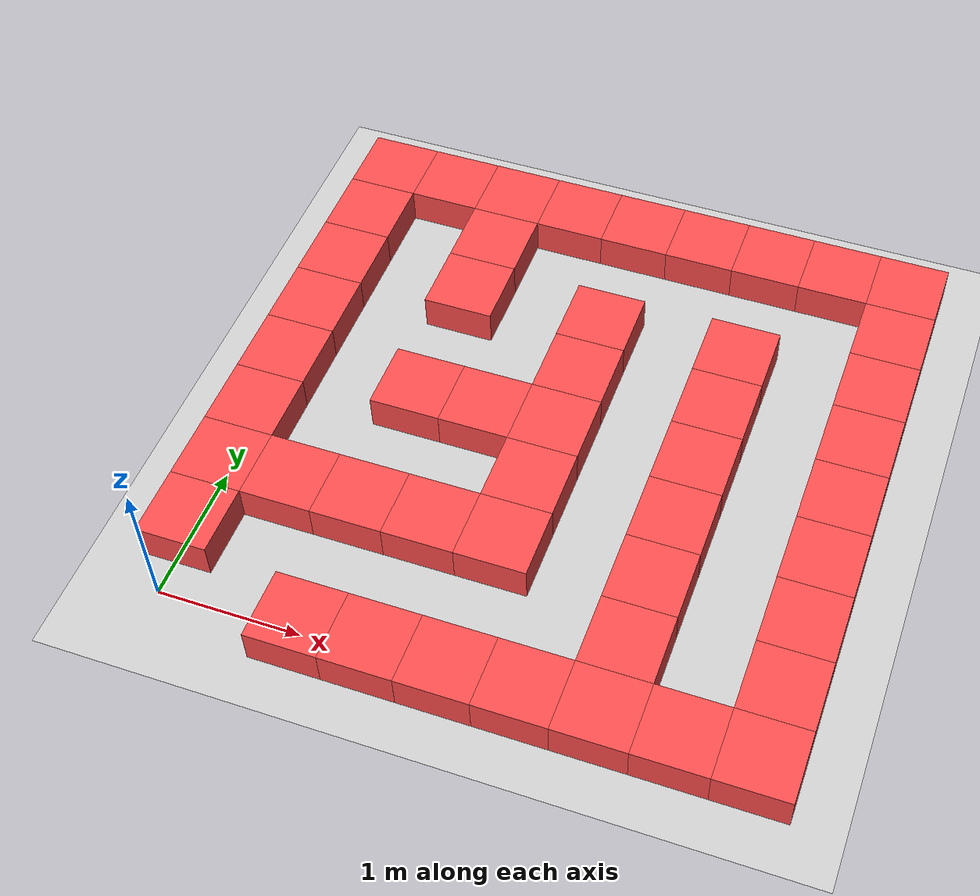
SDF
<sdf version='1.6'>
	<world name='default'>
		<scene>
			<ambient>0.4 0.4 0.4 1</ambient>
			<background>0.7 0.7 0.7 1</background>
			<shadows>1</shadows>
		</scene>
		<light type='directional' name='sun'>
			<cast_shadows>1</cast_shadows>
			<pose frame=''>0 0 10 0 0 0</pose>
			<diffuse>0.8 0.8 0.8 1</diffuse>
			<specular>0.1 0.1 0.1 1</specular>
			<direction>-0.5 0.5 -1</direction>
		</light>
		<gui fullscreen='0'>
			<camera name='user_camera'>
				<pose frame=''>0.027731 -6.7828 1.07118 0 0.016872 1.50135</pose>
				<view_controller>orbit</view_controller>
				<projection_type>perspective</projection_type>
			</camera>
		</gui>
		<model name='ground_plane'>
			<static>1</static>
			<link name='link'>
				<collision name='collision'>
					<geometry>
						<plane>
							<normal>0 0 1</normal>
							<size>100 100</size>
						</plane>
					</geometry>
					<surface>
						<friction>
							<ode>
								<mu>100</mu>
								<mu2>50</mu2>
							</ode>
							<torsional>
								<ode/>
							</torsional>
						</friction>
						<contact>
							<ode/>
						</contact>
						<bounce/>
					</surface>
					<max_contacts>10</max_contacts>
				</collision>
				<visual name='visual'>
					<cast_shadows>0</cast_shadows>
					<geometry>
						<plane>
							<normal>0 0 1</normal>
							<size>100 100</size>
						</plane>
					</geometry>
					<material>
						<script>
							<uri>file://media/materials/scripts/gazebo.material</uri>
							<name>Gazebo/Grey</name>
						</script>
					</material>
				</visual>
			</link>
		</model>
		<physics type='ode' default='0' name='default_physics'>
			<max_step_size>0.001</max_step_size>
			<real_time_factor>1</real_time_factor>
			<real_time_update_rate>1000</real_time_update_rate>
		</physics>
		<gravity>0 0 -9.8</gravity>
		<magnetic_field>6e-06 2.3e-05 -4.2e-05</magnetic_field>
		<atmosphere type='adiabatic'/>
		<spherical_coordinates>
			<surface_model>EARTH_WGS84</surface_model>
			<latitude_deg>0</latitude_deg>
			<longitude_deg>0</longitude_deg>
			<elevation>0</elevation>
			<heading_deg>0</heading_deg>
		</spherical_coordinates>
		<model name='Box_Red_1'>
			<link name='link_0'>
				<pose frame=''>0 0 0 0 -0 0</pose>
				<inertial>
					<mass>1</mass>
					<inertia>
						<ixx>0.166667</ixx>
						<ixy>0</ixy>
						<ixz>0</ixz>
						<iyy>0.166667</iyy>
						<iyz>0</iyz>
						<izz>0.166667</izz>
					</inertia>
					<pose frame=''>0 0 0 0 -0 0</pose>
				</inertial>
				<self_collide>0</self_collide>
				<kinematic>0</kinematic>
				<gravity>1</gravity>
				<visual name='visual'>
					<pose frame=''>0 0 0 0 -0 0</pose>
					<geometry>
						<box>
							<size>0.5 0.5 0.5</size>
						</box>
					</geometry>
					<material>
						<lighting>1</lighting>
						<script>
							<uri>file://media/materials/scripts/gazebo.material</uri>
							<name>Gazebo/Grey</name>
						</script>
						<ambient>1 0.3 0.3 1</ambient>
						<diffuse>0.7 0.7 0.7 1</diffuse>
						<specular>0.01 0.01 0.01 1</specular>
						<emissive>0 0 0 1</emissive>
						<shader type='vertex'>
							<normal_map>__default__</normal_map>
						</shader>
					</material>
					<transparency>0</transparency>
					<cast_shadows>1</cast_shadows>
				</visual>
				<collision name='collision'>
					<laser_retro>0</laser_retro>
					<max_contacts>10</max_contacts>
					<pose frame=''>0 0 0 0 -0 0</pose>
					<geometry>
						<box>
							<size>0.5 0.5 0.5</size>
						</box>
					</geometry>
					<surface>
						<friction>
							<ode>
								<mu>1</mu>
								<mu2>1</mu2>
								<fdir1>0 0 0</fdir1>
								<slip1>0</slip1>
								<slip2>0</slip2>
							</ode>
							<torsional>
								<coefficient>1</coefficient>
								<patch_radius>0</patch_radius>
								<surface_radius>0</surface_radius>
								<use_patch_radius>1</use_patch_radius>
								<ode>
									<slip>0</slip>
								</ode>
							</torsional>
						</friction>
						<bounce>
							<restitution_coefficient>0</restitution_coefficient>
							<threshold>1e+06</threshold>
						</bounce>
						<contact>
							<collide_without_contact>0</collide_without_contact>
							<collide_without_contact_bitmask>1</collide_without_contact_bitmask>
							<collide_bitmask>1</collide_bitmask>
							<ode>
								<soft_cfm>0</soft_cfm>
								<soft_erp>0.2</soft_erp>
								<kp>1e+13</kp>
								<kd>1</kd>
								<max_vel>0.01</max_vel>
								<min_depth>0</min_depth>
							</ode>
							<bullet>
								<split_impulse>1</split_impulse>
								<split_impulse_penetration_threshold>-0.01</split_impulse_penetration_threshold>
								<soft_cfm>0</soft_cfm>
								<soft_erp>0.2</soft_erp>
								<kp>1e+13</kp>
								<kd>1</kd>
							</bullet>
						</contact>
					</surface>
				</collision>
				<enable_wind>0</enable_wind>
			</link>
			<static>0</static>
			<allow_auto_disable>1</allow_auto_disable>
			<pose frame=''>0.000 0.500 0.000 0 0 0</pose>
		</model>
		<model name='Box_Red_2'>
			<link name='link_0'>
				<pose frame=''>0 0 0 0 -0 0</pose>
				<inertial>
					<mass>1</mass>
					<inertia>
						<ixx>0.166667</ixx>
						<ixy>0</ixy>
						<ixz>0</ixz>
						<iyy>0.166667</iyy>
						<iyz>0</iyz>
						<izz>0.166667</izz>
					</inertia>
					<pose frame=''>0 0 0 0 -0 0</pose>
				</inertial>
				<self_collide>0</self_collide>
				<kinematic>0</kinematic>
				<gravity>1</gravity>
				<visual name='visual'>
					<pose frame=''>0 0 0 0 -0 0</pose>
					<geometry>
						<box>
							<size>0.5 0.5 0.5</size>
						</box>
					</geometry>
					<material>
						<lighting>1</lighting>
						<script>
							<uri>file://media/materials/scripts/gazebo.material</uri>
							<name>Gazebo/Grey</name>
						</script>
						<ambient>1 0.3 0.3 1</ambient>
						<diffuse>0.7 0.7 0.7 1</diffuse>
						<specular>0.01 0.01 0.01 1</specular>
						<emissive>0 0 0 1</emissive>
						<shader type='vertex'>
							<normal_map>__default__</normal_map>
						</shader>
					</material>
					<transparency>0</transparency>
					<cast_shadows>1</cast_shadows>
				</visual>
				<collision name='collision'>
					<laser_retro>0</laser_retro>
					<max_contacts>10</max_contacts>
					<pose frame=''>0 0 0 0 -0 0</pose>
					<geometry>
						<box>
							<size>0.5 0.5 0.5</size>
						</box>
					</geometry>
					<surface>
						<friction>
							<ode>
								<mu>1</mu>
								<mu2>1</mu2>
								<fdir1>0 0 0</fdir1>
								<slip1>0</slip1>
								<slip2>0</slip2>
							</ode>
							<torsional>
								<coefficient>1</coefficient>
								<patch_radius>0</patch_radius>
								<surface_radius>0</surface_radius>
								<use_patch_radius>1</use_patch_radius>
								<ode>
									<slip>0</slip>
								</ode>
							</torsional>
						</friction>
						<bounce>
							<restitution_coefficient>0</restitution_coefficient>
							<threshold>1e+06</threshold>
						</bounce>
						<contact>
							<collide_without_contact>0</collide_without_contact>
							<collide_without_contact_bitmask>1</collide_without_contact_bitmask>
							<collide_bitmask>1</collide_bitmask>
							<ode>
								<soft_cfm>0</soft_cfm>
								<soft_erp>0.2</soft_erp>
								<kp>1e+13</kp>
								<kd>1</kd>
								<max_vel>0.01</max_vel>
								<min_depth>0</min_depth>
							</ode>
							<bullet>
								<split_impulse>1</split_impulse>
								<split_impulse_penetration_threshold>-0.01</split_impulse_penetration_threshold>
								<soft_cfm>0</soft_cfm>
								<soft_erp>0.2</soft_erp>
								<kp>1e+13</kp>
								<kd>1</kd>
							</bullet>
						</contact>
					</surface>
				</collision>
				<enable_wind>0</enable_wind>
			</link>
			<static>0</static>
			<allow_auto_disable>1</allow_auto_disable>
			<pose frame=''>0.000 1.000 0.000 0 0 0</pose>
		</model>
		<model name='Box_Red_3'>
			<link name='link_0'>
				<pose frame=''>0 0 0 0 -0 0</pose>
				<inertial>
					<mass>1</mass>
					<inertia>
						<ixx>0.166667</ixx>
						<ixy>0</ixy>
						<ixz>0</ixz>
						<iyy>0.166667</iyy>
						<iyz>0</iyz>
						<izz>0.166667</izz>
					</inertia>
					<pose frame=''>0 0 0 0 -0 0</pose>
				</inertial>
				<self_collide>0</self_collide>
				<kinematic>0</kinematic>
				<gravity>1</gravity>
				<visual name='visual'>
					<pose frame=''>0 0 0 0 -0 0</pose>
					<geometry>
						<box>
							<size>0.5 0.5 0.5</size>
						</box>
					</geometry>
					<material>
						<lighting>1</lighting>
						<script>
							<uri>file://media/materials/scripts/gazebo.material</uri>
							<name>Gazebo/Grey</name>
						</script>
						<ambient>1 0.3 0.3 1</ambient>
						<diffuse>0.7 0.7 0.7 1</diffuse>
						<specular>0.01 0.01 0.01 1</specular>
						<emissive>0 0 0 1</emissive>
						<shader type='vertex'>
							<normal_map>__default__</normal_map>
						</shader>
					</material>
					<transparency>0</transparency>
					<cast_shadows>1</cast_shadows>
				</visual>
				<collision name='collision'>
					<laser_retro>0</laser_retro>
					<max_contacts>10</max_contacts>
					<pose frame=''>0 0 0 0 -0 0</pose>
					<geometry>
						<box>
							<size>0.5 0.5 0.5</size>
						</box>
					</geometry>
					<surface>
						<friction>
							<ode>
								<mu>1</mu>
								<mu2>1</mu2>
								<fdir1>0 0 0</fdir1>
								<slip1>0</slip1>
								<slip2>0</slip2>
							</ode>
							<torsional>
								<coefficient>1</coefficient>
								<patch_radius>0</patch_radius>
								<surface_radius>0</surface_radius>
								<use_patch_radius>1</use_patch_radius>
								<ode>
									<slip>0</slip>
								</ode>
							</torsional>
						</friction>
						<bounce>
							<restitution_coefficient>0</restitution_coefficient>
							<threshold>1e+06</threshold>
						</bounce>
						<contact>
							<collide_without_contact>0</collide_without_contact>
							<collide_without_contact_bitmask>1</collide_without_contact_bitmask>
							<collide_bitmask>1</collide_bitmask>
							<ode>
								<soft_cfm>0</soft_cfm>
								<soft_erp>0.2</soft_erp>
								<kp>1e+13</kp>
								<kd>1</kd>
								<max_vel>0.01</max_vel>
								<min_depth>0</min_depth>
							</ode>
							<bullet>
								<split_impulse>1</split_impulse>
								<split_impulse_penetration_threshold>-0.01</split_impulse_penetration_threshold>
								<soft_cfm>0</soft_cfm>
								<soft_erp>0.2</soft_erp>
								<kp>1e+13</kp>
								<kd>1</kd>
							</bullet>
						</contact>
					</surface>
				</collision>
				<enable_wind>0</enable_wind>
			</link>
			<static>0</static>
			<allow_auto_disable>1</allow_auto_disable>
			<pose frame=''>0.000 1.500 0.000 0 0 0</pose>
		</model>
		<model name='Box_Red_4'>
			<link name='link_0'>
				<pose frame=''>0 0 0 0 -0 0</pose>
				<inertial>
					<mass>1</mass>
					<inertia>
						<ixx>0.166667</ixx>
						<ixy>0</ixy>
						<ixz>0</ixz>
						<iyy>0.166667</iyy>
						<iyz>0</iyz>
						<izz>0.166667</izz>
					</inertia>
					<pose frame=''>0 0 0 0 -0 0</pose>
				</inertial>
				<self_collide>0</self_collide>
				<kinematic>0</kinematic>
				<gravity>1</gravity>
				<visual name='visual'>
					<pose frame=''>0 0 0 0 -0 0</pose>
					<geometry>
						<box>
							<size>0.5 0.5 0.5</size>
						</box>
					</geometry>
					<material>
						<lighting>1</lighting>
						<script>
							<uri>file://media/materials/scripts/gazebo.material</uri>
							<name>Gazebo/Grey</name>
						</script>
						<ambient>1 0.3 0.3 1</ambient>
						<diffuse>0.7 0.7 0.7 1</diffuse>
						<specular>0.01 0.01 0.01 1</specular>
						<emissive>0 0 0 1</emissive>
						<shader type='vertex'>
							<normal_map>__default__</normal_map>
						</shader>
					</material>
					<transparency>0</transparency>
					<cast_shadows>1</cast_shadows>
				</visual>
				<collision name='collision'>
					<laser_retro>0</laser_retro>
					<max_contacts>10</max_contacts>
					<pose frame=''>0 0 0 0 -0 0</pose>
					<geometry>
						<box>
							<size>0.5 0.5 0.5</size>
						</box>
					</geometry>
					<surface>
						<friction>
							<ode>
								<mu>1</mu>
								<mu2>1</mu2>
								<fdir1>0 0 0</fdir1>
								<slip1>0</slip1>
								<slip2>0</slip2>
							</ode>
							<torsional>
								<coefficient>1</coefficient>
								<patch_radius>0</patch_radius>
								<surface_radius>0</surface_radius>
								<use_patch_radius>1</use_patch_radius>
								<ode>
									<slip>0</slip>
								</ode>
							</torsional>
						</friction>
						<bounce>
							<restitution_coefficient>0</restitution_coefficient>
							<threshold>1e+06</threshold>
						</bounce>
						<contact>
							<collide_without_contact>0</collide_without_contact>
							<collide_without_contact_bitmask>1</collide_without_contact_bitmask>
							<collide_bitmask>1</collide_bitmask>
							<ode>
								<soft_cfm>0</soft_cfm>
								<soft_erp>0.2</soft_erp>
								<kp>1e+13</kp>
								<kd>1</kd>
								<max_vel>0.01</max_vel>
								<min_depth>0</min_depth>
							</ode>
							<bullet>
								<split_impulse>1</split_impulse>
								<split_impulse_penetration_threshold>-0.01</split_impulse_penetration_threshold>
								<soft_cfm>0</soft_cfm>
								<soft_erp>0.2</soft_erp>
								<kp>1e+13</kp>
								<kd>1</kd>
							</bullet>
						</contact>
					</surface>
				</collision>
				<enable_wind>0</enable_wind>
			</link>
			<static>0</static>
			<allow_auto_disable>1</allow_auto_disable>
			<pose frame=''>0.000 2.000 0.000 0 0 0</pose>
		</model>
		<model name='Box_Red_5'>
			<link name='link_0'>
				<pose frame=''>0 0 0 0 -0 0</pose>
				<inertial>
					<mass>1</mass>
					<inertia>
						<ixx>0.166667</ixx>
						<ixy>0</ixy>
						<ixz>0</ixz>
						<iyy>0.166667</iyy>
						<iyz>0</iyz>
						<izz>0.166667</izz>
					</inertia>
					<pose frame=''>0 0 0 0 -0 0</pose>
				</inertial>
				<self_collide>0</self_collide>
				<kinematic>0</kinematic>
				<gravity>1</gravity>
				<visual name='visual'>
					<pose frame=''>0 0 0 0 -0 0</pose>
					<geometry>
						<box>
							<size>0.5 0.5 0.5</size>
						</box>
					</geometry>
					<material>
						<lighting>1</lighting>
						<script>
							<uri>file://media/materials/scripts/gazebo.material</uri>
							<name>Gazebo/Grey</name>
						</script>
						<ambient>1 0.3 0.3 1</ambient>
						<diffuse>0.7 0.7 0.7 1</diffuse>
						<specular>0.01 0.01 0.01 1</specular>
						<emissive>0 0 0 1</emissive>
						<shader type='vertex'>
							<normal_map>__default__</normal_map>
						</shader>
					</material>
					<transparency>0</transparency>
					<cast_shadows>1</cast_shadows>
				</visual>
				<collision name='collision'>
					<laser_retro>0</laser_retro>
					<max_contacts>10</max_contacts>
					<pose frame=''>0 0 0 0 -0 0</pose>
					<geometry>
						<box>
							<size>0.5 0.5 0.5</size>
						</box>
					</geometry>
					<surface>
						<friction>
							<ode>
								<mu>1</mu>
								<mu2>1</mu2>
								<fdir1>0 0 0</fdir1>
								<slip1>0</slip1>
								<slip2>0</slip2>
							</ode>
							<torsional>
								<coefficient>1</coefficient>
								<patch_radius>0</patch_radius>
								<surface_radius>0</surface_radius>
								<use_patch_radius>1</use_patch_radius>
								<ode>
									<slip>0</slip>
								</ode>
							</torsional>
						</friction>
						<bounce>
							<restitution_coefficient>0</restitution_coefficient>
							<threshold>1e+06</threshold>
						</bounce>
						<contact>
							<collide_without_contact>0</collide_without_contact>
							<collide_without_contact_bitmask>1</collide_without_contact_bitmask>
							<collide_bitmask>1</collide_bitmask>
							<ode>
								<soft_cfm>0</soft_cfm>
								<soft_erp>0.2</soft_erp>
								<kp>1e+13</kp>
								<kd>1</kd>
								<max_vel>0.01</max_vel>
								<min_depth>0</min_depth>
							</ode>
							<bullet>
								<split_impulse>1</split_impulse>
								<split_impulse_penetration_threshold>-0.01</split_impulse_penetration_threshold>
								<soft_cfm>0</soft_cfm>
								<soft_erp>0.2</soft_erp>
								<kp>1e+13</kp>
								<kd>1</kd>
							</bullet>
						</contact>
					</surface>
				</collision>
				<enable_wind>0</enable_wind>
			</link>
			<static>0</static>
			<allow_auto_disable>1</allow_auto_disable>
			<pose frame=''>0.000 2.500 0.000 0 0 0</pose>
		</model>
		<model name='Box_Red_6'>
			<link name='link_0'>
				<pose frame=''>0 0 0 0 -0 0</pose>
				<inertial>
					<mass>1</mass>
					<inertia>
						<ixx>0.166667</ixx>
						<ixy>0</ixy>
						<ixz>0</ixz>
						<iyy>0.166667</iyy>
						<iyz>0</iyz>
						<izz>0.166667</izz>
					</inertia>
					<pose frame=''>0 0 0 0 -0 0</pose>
				</inertial>
				<self_collide>0</self_collide>
				<kinematic>0</kinematic>
				<gravity>1</gravity>
				<visual name='visual'>
					<pose frame=''>0 0 0 0 -0 0</pose>
					<geometry>
						<box>
							<size>0.5 0.5 0.5</size>
						</box>
					</geometry>
					<material>
						<lighting>1</lighting>
						<script>
							<uri>file://media/materials/scripts/gazebo.material</uri>
							<name>Gazebo/Grey</name>
						</script>
						<ambient>1 0.3 0.3 1</ambient>
						<diffuse>0.7 0.7 0.7 1</diffuse>
						<specular>0.01 0.01 0.01 1</specular>
						<emissive>0 0 0 1</emissive>
						<shader type='vertex'>
							<normal_map>__default__</normal_map>
						</shader>
					</material>
					<transparency>0</transparency>
					<cast_shadows>1</cast_shadows>
				</visual>
				<collision name='collision'>
					<laser_retro>0</laser_retro>
					<max_contacts>10</max_contacts>
					<pose frame=''>0 0 0 0 -0 0</pose>
					<geometry>
						<box>
							<size>0.5 0.5 0.5</size>
						</box>
					</geometry>
					<surface>
						<friction>
							<ode>
								<mu>1</mu>
								<mu2>1</mu2>
								<fdir1>0 0 0</fdir1>
								<slip1>0</slip1>
								<slip2>0</slip2>
							</ode>
							<torsional>
								<coefficient>1</coefficient>
								<patch_radius>0</patch_radius>
								<surface_radius>0</surface_radius>
								<use_patch_radius>1</use_patch_radius>
								<ode>
									<slip>0</slip>
								</ode>
							</torsional>
						</friction>
						<bounce>
							<restitution_coefficient>0</restitution_coefficient>
							<threshold>1e+06</threshold>
						</bounce>
						<contact>
							<collide_without_contact>0</collide_without_contact>
							<collide_without_contact_bitmask>1</collide_without_contact_bitmask>
							<collide_bitmask>1</collide_bitmask>
							<ode>
								<soft_cfm>0</soft_cfm>
								<soft_erp>0.2</soft_erp>
								<kp>1e+13</kp>
								<kd>1</kd>
								<max_vel>0.01</max_vel>
								<min_depth>0</min_depth>
							</ode>
							<bullet>
								<split_impulse>1</split_impulse>
								<split_impulse_penetration_threshold>-0.01</split_impulse_penetration_threshold>
								<soft_cfm>0</soft_cfm>
								<soft_erp>0.2</soft_erp>
								<kp>1e+13</kp>
								<kd>1</kd>
							</bullet>
						</contact>
					</surface>
				</collision>
				<enable_wind>0</enable_wind>
			</link>
			<static>0</static>
			<allow_auto_disable>1</allow_auto_disable>
			<pose frame=''>0.000 3.000 0.000 0 0 0</pose>
		</model>
		<model name='Box_Red_7'>
			<link name='link_0'>
				<pose frame=''>0 0 0 0 -0 0</pose>
				<inertial>
					<mass>1</mass>
					<inertia>
						<ixx>0.166667</ixx>
						<ixy>0</ixy>
						<ixz>0</ixz>
						<iyy>0.166667</iyy>
						<iyz>0</iyz>
						<izz>0.166667</izz>
					</inertia>
					<pose frame=''>0 0 0 0 -0 0</pose>
				</inertial>
				<self_collide>0</self_collide>
				<kinematic>0</kinematic>
				<gravity>1</gravity>
				<visual name='visual'>
					<pose frame=''>0 0 0 0 -0 0</pose>
					<geometry>
						<box>
							<size>0.5 0.5 0.5</size>
						</box>
					</geometry>
					<material>
						<lighting>1</lighting>
						<script>
							<uri>file://media/materials/scripts/gazebo.material</uri>
							<name>Gazebo/Grey</name>
						</script>
						<ambient>1 0.3 0.3 1</ambient>
						<diffuse>0.7 0.7 0.7 1</diffuse>
						<specular>0.01 0.01 0.01 1</specular>
						<emissive>0 0 0 1</emissive>
						<shader type='vertex'>
							<normal_map>__default__</normal_map>
						</shader>
					</material>
					<transparency>0</transparency>
					<cast_shadows>1</cast_shadows>
				</visual>
				<collision name='collision'>
					<laser_retro>0</laser_retro>
					<max_contacts>10</max_contacts>
					<pose frame=''>0 0 0 0 -0 0</pose>
					<geometry>
						<box>
							<size>0.5 0.5 0.5</size>
						</box>
					</geometry>
					<surface>
						<friction>
							<ode>
								<mu>1</mu>
								<mu2>1</mu2>
								<fdir1>0 0 0</fdir1>
								<slip1>0</slip1>
								<slip2>0</slip2>
							</ode>
							<torsional>
								<coefficient>1</coefficient>
								<patch_radius>0</patch_radius>
								<surface_radius>0</surface_radius>
								<use_patch_radius>1</use_patch_radius>
								<ode>
									<slip>0</slip>
								</ode>
							</torsional>
						</friction>
						<bounce>
							<restitution_coefficient>0</restitution_coefficient>
							<threshold>1e+06</threshold>
						</bounce>
						<contact>
							<collide_without_contact>0</collide_without_contact>
							<collide_without_contact_bitmask>1</collide_without_contact_bitmask>
							<collide_bitmask>1</collide_bitmask>
							<ode>
								<soft_cfm>0</soft_cfm>
								<soft_erp>0.2</soft_erp>
								<kp>1e+13</kp>
								<kd>1</kd>
								<max_vel>0.01</max_vel>
								<min_depth>0</min_depth>
							</ode>
							<bullet>
								<split_impulse>1</split_impulse>
								<split_impulse_penetration_threshold>-0.01</split_impulse_penetration_threshold>
								<soft_cfm>0</soft_cfm>
								<soft_erp>0.2</soft_erp>
								<kp>1e+13</kp>
								<kd>1</kd>
							</bullet>
						</contact>
					</surface>
				</collision>
				<enable_wind>0</enable_wind>
			</link>
			<static>0</static>
			<allow_auto_disable>1</allow_auto_disable>
			<pose frame=''>0.000 3.500 0.000 0 0 0</pose>
		</model>
		<model name='Box_Red_8'>
			<link name='link_0'>
				<pose frame=''>0 0 0 0 -0 0</pose>
				<inertial>
					<mass>1</mass>
					<inertia>
						<ixx>0.166667</ixx>
						<ixy>0</ixy>
						<ixz>0</ixz>
						<iyy>0.166667</iyy>
						<iyz>0</iyz>
						<izz>0.166667</izz>
					</inertia>
					<pose frame=''>0 0 0 0 -0 0</pose>
				</inertial>
				<self_collide>0</self_collide>
				<kinematic>0</kinematic>
				<gravity>1</gravity>
				<visual name='visual'>
					<pose frame=''>0 0 0 0 -0 0</pose>
					<geometry>
						<box>
							<size>0.5 0.5 0.5</size>
						</box>
					</geometry>
					<material>
						<lighting>1</lighting>
						<script>
							<uri>file://media/materials/scripts/gazebo.material</uri>
							<name>Gazebo/Grey</name>
						</script>
						<ambient>1 0.3 0.3 1</ambient>
						<diffuse>0.7 0.7 0.7 1</diffuse>
						<specular>0.01 0.01 0.01 1</specular>
						<emissive>0 0 0 1</emissive>
						<shader type='vertex'>
							<normal_map>__default__</normal_map>
						</shader>
					</material>
					<transparency>0</transparency>
					<cast_shadows>1</cast_shadows>
				</visual>
				<collision name='collision'>
					<laser_retro>0</laser_retro>
					<max_contacts>10</max_contacts>
					<pose frame=''>0 0 0 0 -0 0</pose>
					<geometry>
						<box>
							<size>0.5 0.5 0.5</size>
						</box>
					</geometry>
					<surface>
						<friction>
							<ode>
								<mu>1</mu>
								<mu2>1</mu2>
								<fdir1>0 0 0</fdir1>
								<slip1>0</slip1>
								<slip2>0</slip2>
							</ode>
							<torsional>
								<coefficient>1</coefficient>
								<patch_radius>0</patch_radius>
								<surface_radius>0</surface_radius>
								<use_patch_radius>1</use_patch_radius>
								<ode>
									<slip>0</slip>
								</ode>
							</torsional>
						</friction>
						<bounce>
							<restitution_coefficient>0</restitution_coefficient>
							<threshold>1e+06</threshold>
						</bounce>
						<contact>
							<collide_without_contact>0</collide_without_contact>
							<collide_without_contact_bitmask>1</collide_without_contact_bitmask>
							<collide_bitmask>1</collide_bitmask>
							<ode>
								<soft_cfm>0</soft_cfm>
								<soft_erp>0.2</soft_erp>
								<kp>1e+13</kp>
								<kd>1</kd>
								<max_vel>0.01</max_vel>
								<min_depth>0</min_depth>
							</ode>
							<bullet>
								<split_impulse>1</split_impulse>
								<split_impulse_penetration_threshold>-0.01</split_impulse_penetration_threshold>
								<soft_cfm>0</soft_cfm>
								<soft_erp>0.2</soft_erp>
								<kp>1e+13</kp>
								<kd>1</kd>
							</bullet>
						</contact>
					</surface>
				</collision>
				<enable_wind>0</enable_wind>
			</link>
			<static>0</static>
			<allow_auto_disable>1</allow_auto_disable>
			<pose frame=''>0.000 4.000 0.000 0 0 0</pose>
		</model>
		<model name='Box_Red_11'>
			<link name='link_0'>
				<pose frame=''>0 0 0 0 -0 0</pose>
				<inertial>
					<mass>1</mass>
					<inertia>
						<ixx>0.166667</ixx>
						<ixy>0</ixy>
						<ixz>0</ixz>
						<iyy>0.166667</iyy>
						<iyz>0</iyz>
						<izz>0.166667</izz>
					</inertia>
					<pose frame=''>0 0 0 0 -0 0</pose>
				</inertial>
				<self_collide>0</self_collide>
				<kinematic>0</kinematic>
				<gravity>1</gravity>
				<visual name='visual'>
					<pose frame=''>0 0 0 0 -0 0</pose>
					<geometry>
						<box>
							<size>0.5 0.5 0.5</size>
						</box>
					</geometry>
					<material>
						<lighting>1</lighting>
						<script>
							<uri>file://media/materials/scripts/gazebo.material</uri>
							<name>Gazebo/Grey</name>
						</script>
						<ambient>1 0.3 0.3 1</ambient>
						<diffuse>0.7 0.7 0.7 1</diffuse>
						<specular>0.01 0.01 0.01 1</specular>
						<emissive>0 0 0 1</emissive>
						<shader type='vertex'>
							<normal_map>__default__</normal_map>
						</shader>
					</material>
					<transparency>0</transparency>
					<cast_shadows>1</cast_shadows>
				</visual>
				<collision name='collision'>
					<laser_retro>0</laser_retro>
					<max_contacts>10</max_contacts>
					<pose frame=''>0 0 0 0 -0 0</pose>
					<geometry>
						<box>
							<size>0.5 0.5 0.5</size>
						</box>
					</geometry>
					<surface>
						<friction>
							<ode>
								<mu>1</mu>
								<mu2>1</mu2>
								<fdir1>0 0 0</fdir1>
								<slip1>0</slip1>
								<slip2>0</slip2>
							</ode>
							<torsional>
								<coefficient>1</coefficient>
								<patch_radius>0</patch_radius>
								<surface_radius>0</surface_radius>
								<use_patch_radius>1</use_patch_radius>
								<ode>
									<slip>0</slip>
								</ode>
							</torsional>
						</friction>
						<bounce>
							<restitution_coefficient>0</restitution_coefficient>
							<threshold>1e+06</threshold>
						</bounce>
						<contact>
							<collide_without_contact>0</collide_without_contact>
							<collide_without_contact_bitmask>1</collide_without_contact_bitmask>
							<collide_bitmask>1</collide_bitmask>
							<ode>
								<soft_cfm>0</soft_cfm>
								<soft_erp>0.2</soft_erp>
								<kp>1e+13</kp>
								<kd>1</kd>
								<max_vel>0.01</max_vel>
								<min_depth>0</min_depth>
							</ode>
							<bullet>
								<split_impulse>1</split_impulse>
								<split_impulse_penetration_threshold>-0.01</split_impulse_penetration_threshold>
								<soft_cfm>0</soft_cfm>
								<soft_erp>0.2</soft_erp>
								<kp>1e+13</kp>
								<kd>1</kd>
							</bullet>
						</contact>
					</surface>
				</collision>
				<enable_wind>0</enable_wind>
			</link>
			<static>0</static>
			<allow_auto_disable>1</allow_auto_disable>
			<pose frame=''>0.500 1.000 0.000 0 0 0</pose>
		</model>
		<model name='Box_Red_17'>
			<link name='link_0'>
				<pose frame=''>0 0 0 0 -0 0</pose>
				<inertial>
					<mass>1</mass>
					<inertia>
						<ixx>0.166667</ixx>
						<ixy>0</ixy>
						<ixz>0</ixz>
						<iyy>0.166667</iyy>
						<iyz>0</iyz>
						<izz>0.166667</izz>
					</inertia>
					<pose frame=''>0 0 0 0 -0 0</pose>
				</inertial>
				<self_collide>0</self_collide>
				<kinematic>0</kinematic>
				<gravity>1</gravity>
				<visual name='visual'>
					<pose frame=''>0 0 0 0 -0 0</pose>
					<geometry>
						<box>
							<size>0.5 0.5 0.5</size>
						</box>
					</geometry>
					<material>
						<lighting>1</lighting>
						<script>
							<uri>file://media/materials/scripts/gazebo.material</uri>
							<name>Gazebo/Grey</name>
						</script>
						<ambient>1 0.3 0.3 1</ambient>
						<diffuse>0.7 0.7 0.7 1</diffuse>
						<specular>0.01 0.01 0.01 1</specular>
						<emissive>0 0 0 1</emissive>
						<shader type='vertex'>
							<normal_map>__default__</normal_map>
						</shader>
					</material>
					<transparency>0</transparency>
					<cast_shadows>1</cast_shadows>
				</visual>
				<collision name='collision'>
					<laser_retro>0</laser_retro>
					<max_contacts>10</max_contacts>
					<pose frame=''>0 0 0 0 -0 0</pose>
					<geometry>
						<box>
							<size>0.5 0.5 0.5</size>
						</box>
					</geometry>
					<surface>
						<friction>
							<ode>
								<mu>1</mu>
								<mu2>1</mu2>
								<fdir1>0 0 0</fdir1>
								<slip1>0</slip1>
								<slip2>0</slip2>
							</ode>
							<torsional>
								<coefficient>1</coefficient>
								<patch_radius>0</patch_radius>
								<surface_radius>0</surface_radius>
								<use_patch_radius>1</use_patch_radius>
								<ode>
									<slip>0</slip>
								</ode>
							</torsional>
						</friction>
						<bounce>
							<restitution_coefficient>0</restitution_coefficient>
							<threshold>1e+06</threshold>
						</bounce>
						<contact>
							<collide_without_contact>0</collide_without_contact>
							<collide_without_contact_bitmask>1</collide_without_contact_bitmask>
							<collide_bitmask>1</collide_bitmask>
							<ode>
								<soft_cfm>0</soft_cfm>
								<soft_erp>0.2</soft_erp>
								<kp>1e+13</kp>
								<kd>1</kd>
								<max_vel>0.01</max_vel>
								<min_depth>0</min_depth>
							</ode>
							<bullet>
								<split_impulse>1</split_impulse>
								<split_impulse_penetration_threshold>-0.01</split_impulse_penetration_threshold>
								<soft_cfm>0</soft_cfm>
								<soft_erp>0.2</soft_erp>
								<kp>1e+13</kp>
								<kd>1</kd>
							</bullet>
						</contact>
					</surface>
				</collision>
				<enable_wind>0</enable_wind>
			</link>
			<static>0</static>
			<allow_auto_disable>1</allow_auto_disable>
			<pose frame=''>0.500 4.000 0.000 0 0 0</pose>
		</model>
		<model name='Box_Red_18'>
			<link name='link_0'>
				<pose frame=''>0 0 0 0 -0 0</pose>
				<inertial>
					<mass>1</mass>
					<inertia>
						<ixx>0.166667</ixx>
						<ixy>0</ixy>
						<ixz>0</ixz>
						<iyy>0.166667</iyy>
						<iyz>0</iyz>
						<izz>0.166667</izz>
					</inertia>
					<pose frame=''>0 0 0 0 -0 0</pose>
				</inertial>
				<self_collide>0</self_collide>
				<kinematic>0</kinematic>
				<gravity>1</gravity>
				<visual name='visual'>
					<pose frame=''>0 0 0 0 -0 0</pose>
					<geometry>
						<box>
							<size>0.5 0.5 0.5</size>
						</box>
					</geometry>
					<material>
						<lighting>1</lighting>
						<script>
							<uri>file://media/materials/scripts/gazebo.material</uri>
							<name>Gazebo/Grey</name>
						</script>
						<ambient>1 0.3 0.3 1</ambient>
						<diffuse>0.7 0.7 0.7 1</diffuse>
						<specular>0.01 0.01 0.01 1</specular>
						<emissive>0 0 0 1</emissive>
						<shader type='vertex'>
							<normal_map>__default__</normal_map>
						</shader>
					</material>
					<transparency>0</transparency>
					<cast_shadows>1</cast_shadows>
				</visual>
				<collision name='collision'>
					<laser_retro>0</laser_retro>
					<max_contacts>10</max_contacts>
					<pose frame=''>0 0 0 0 -0 0</pose>
					<geometry>
						<box>
							<size>0.5 0.5 0.5</size>
						</box>
					</geometry>
					<surface>
						<friction>
							<ode>
								<mu>1</mu>
								<mu2>1</mu2>
								<fdir1>0 0 0</fdir1>
								<slip1>0</slip1>
								<slip2>0</slip2>
							</ode>
							<torsional>
								<coefficient>1</coefficient>
								<patch_radius>0</patch_radius>
								<surface_radius>0</surface_radius>
								<use_patch_radius>1</use_patch_radius>
								<ode>
									<slip>0</slip>
								</ode>
							</torsional>
						</friction>
						<bounce>
							<restitution_coefficient>0</restitution_coefficient>
							<threshold>1e+06</threshold>
						</bounce>
						<contact>
							<collide_without_contact>0</collide_without_contact>
							<collide_without_contact_bitmask>1</collide_without_contact_bitmask>
							<collide_bitmask>1</collide_bitmask>
							<ode>
								<soft_cfm>0</soft_cfm>
								<soft_erp>0.2</soft_erp>
								<kp>1e+13</kp>
								<kd>1</kd>
								<max_vel>0.01</max_vel>
								<min_depth>0</min_depth>
							</ode>
							<bullet>
								<split_impulse>1</split_impulse>
								<split_impulse_penetration_threshold>-0.01</split_impulse_penetration_threshold>
								<soft_cfm>0</soft_cfm>
								<soft_erp>0.2</soft_erp>
								<kp>1e+13</kp>
								<kd>1</kd>
							</bullet>
						</contact>
					</surface>
				</collision>
				<enable_wind>0</enable_wind>
			</link>
			<static>0</static>
			<allow_auto_disable>1</allow_auto_disable>
			<pose frame=''>1.000 0.000 0.000 0 0 0</pose>
		</model>
		<model name='Box_Red_20'>
			<link name='link_0'>
				<pose frame=''>0 0 0 0 -0 0</pose>
				<inertial>
					<mass>1</mass>
					<inertia>
						<ixx>0.166667</ixx>
						<ixy>0</ixy>
						<ixz>0</ixz>
						<iyy>0.166667</iyy>
						<iyz>0</iyz>
						<izz>0.166667</izz>
					</inertia>
					<pose frame=''>0 0 0 0 -0 0</pose>
				</inertial>
				<self_collide>0</self_collide>
				<kinematic>0</kinematic>
				<gravity>1</gravity>
				<visual name='visual'>
					<pose frame=''>0 0 0 0 -0 0</pose>
					<geometry>
						<box>
							<size>0.5 0.5 0.5</size>
						</box>
					</geometry>
					<material>
						<lighting>1</lighting>
						<script>
							<uri>file://media/materials/scripts/gazebo.material</uri>
							<name>Gazebo/Grey</name>
						</script>
						<ambient>1 0.3 0.3 1</ambient>
						<diffuse>0.7 0.7 0.7 1</diffuse>
						<specular>0.01 0.01 0.01 1</specular>
						<emissive>0 0 0 1</emissive>
						<shader type='vertex'>
							<normal_map>__default__</normal_map>
						</shader>
					</material>
					<transparency>0</transparency>
					<cast_shadows>1</cast_shadows>
				</visual>
				<collision name='collision'>
					<laser_retro>0</laser_retro>
					<max_contacts>10</max_contacts>
					<pose frame=''>0 0 0 0 -0 0</pose>
					<geometry>
						<box>
							<size>0.5 0.5 0.5</size>
						</box>
					</geometry>
					<surface>
						<friction>
							<ode>
								<mu>1</mu>
								<mu2>1</mu2>
								<fdir1>0 0 0</fdir1>
								<slip1>0</slip1>
								<slip2>0</slip2>
							</ode>
							<torsional>
								<coefficient>1</coefficient>
								<patch_radius>0</patch_radius>
								<surface_radius>0</surface_radius>
								<use_patch_radius>1</use_patch_radius>
								<ode>
									<slip>0</slip>
								</ode>
							</torsional>
						</friction>
						<bounce>
							<restitution_coefficient>0</restitution_coefficient>
							<threshold>1e+06</threshold>
						</bounce>
						<contact>
							<collide_without_contact>0</collide_without_contact>
							<collide_without_contact_bitmask>1</collide_without_contact_bitmask>
							<collide_bitmask>1</collide_bitmask>
							<ode>
								<soft_cfm>0</soft_cfm>
								<soft_erp>0.2</soft_erp>
								<kp>1e+13</kp>
								<kd>1</kd>
								<max_vel>0.01</max_vel>
								<min_depth>0</min_depth>
							</ode>
							<bullet>
								<split_impulse>1</split_impulse>
								<split_impulse_penetration_threshold>-0.01</split_impulse_penetration_threshold>
								<soft_cfm>0</soft_cfm>
								<soft_erp>0.2</soft_erp>
								<kp>1e+13</kp>
								<kd>1</kd>
							</bullet>
						</contact>
					</surface>
				</collision>
				<enable_wind>0</enable_wind>
			</link>
			<static>0</static>
			<allow_auto_disable>1</allow_auto_disable>
			<pose frame=''>1.000 1.000 0.000 0 0 0</pose>
		</model>
		<model name='Box_Red_22'>
			<link name='link_0'>
				<pose frame=''>0 0 0 0 -0 0</pose>
				<inertial>
					<mass>1</mass>
					<inertia>
						<ixx>0.166667</ixx>
						<ixy>0</ixy>
						<ixz>0</ixz>
						<iyy>0.166667</iyy>
						<iyz>0</iyz>
						<izz>0.166667</izz>
					</inertia>
					<pose frame=''>0 0 0 0 -0 0</pose>
				</inertial>
				<self_collide>0</self_collide>
				<kinematic>0</kinematic>
				<gravity>1</gravity>
				<visual name='visual'>
					<pose frame=''>0 0 0 0 -0 0</pose>
					<geometry>
						<box>
							<size>0.5 0.5 0.5</size>
						</box>
					</geometry>
					<material>
						<lighting>1</lighting>
						<script>
							<uri>file://media/materials/scripts/gazebo.material</uri>
							<name>Gazebo/Grey</name>
						</script>
						<ambient>1 0.3 0.3 1</ambient>
						<diffuse>0.7 0.7 0.7 1</diffuse>
						<specular>0.01 0.01 0.01 1</specular>
						<emissive>0 0 0 1</emissive>
						<shader type='vertex'>
							<normal_map>__default__</normal_map>
						</shader>
					</material>
					<transparency>0</transparency>
					<cast_shadows>1</cast_shadows>
				</visual>
				<collision name='collision'>
					<laser_retro>0</laser_retro>
					<max_contacts>10</max_contacts>
					<pose frame=''>0 0 0 0 -0 0</pose>
					<geometry>
						<box>
							<size>0.5 0.5 0.5</size>
						</box>
					</geometry>
					<surface>
						<friction>
							<ode>
								<mu>1</mu>
								<mu2>1</mu2>
								<fdir1>0 0 0</fdir1>
								<slip1>0</slip1>
								<slip2>0</slip2>
							</ode>
							<torsional>
								<coefficient>1</coefficient>
								<patch_radius>0</patch_radius>
								<surface_radius>0</surface_radius>
								<use_patch_radius>1</use_patch_radius>
								<ode>
									<slip>0</slip>
								</ode>
							</torsional>
						</friction>
						<bounce>
							<restitution_coefficient>0</restitution_coefficient>
							<threshold>1e+06</threshold>
						</bounce>
						<contact>
							<collide_without_contact>0</collide_without_contact>
							<collide_without_contact_bitmask>1</collide_without_contact_bitmask>
							<collide_bitmask>1</collide_bitmask>
							<ode>
								<soft_cfm>0</soft_cfm>
								<soft_erp>0.2</soft_erp>
								<kp>1e+13</kp>
								<kd>1</kd>
								<max_vel>0.01</max_vel>
								<min_depth>0</min_depth>
							</ode>
							<bullet>
								<split_impulse>1</split_impulse>
								<split_impulse_penetration_threshold>-0.01</split_impulse_penetration_threshold>
								<soft_cfm>0</soft_cfm>
								<soft_erp>0.2</soft_erp>
								<kp>1e+13</kp>
								<kd>1</kd>
							</bullet>
						</contact>
					</surface>
				</collision>
				<enable_wind>0</enable_wind>
			</link>
			<static>0</static>
			<allow_auto_disable>1</allow_auto_disable>
			<pose frame=''>1.000 2.000 0.000 0 0 0</pose>
		</model>
		<model name='Box_Red_24'>
			<link name='link_0'>
				<pose frame=''>0 0 0 0 -0 0</pose>
				<inertial>
					<mass>1</mass>
					<inertia>
						<ixx>0.166667</ixx>
						<ixy>0</ixy>
						<ixz>0</ixz>
						<iyy>0.166667</iyy>
						<iyz>0</iyz>
						<izz>0.166667</izz>
					</inertia>
					<pose frame=''>0 0 0 0 -0 0</pose>
				</inertial>
				<self_collide>0</self_collide>
				<kinematic>0</kinematic>
				<gravity>1</gravity>
				<visual name='visual'>
					<pose frame=''>0 0 0 0 -0 0</pose>
					<geometry>
						<box>
							<size>0.5 0.5 0.5</size>
						</box>
					</geometry>
					<material>
						<lighting>1</lighting>
						<script>
							<uri>file://media/materials/scripts/gazebo.material</uri>
							<name>Gazebo/Grey</name>
						</script>
						<ambient>1 0.3 0.3 1</ambient>
						<diffuse>0.7 0.7 0.7 1</diffuse>
						<specular>0.01 0.01 0.01 1</specular>
						<emissive>0 0 0 1</emissive>
						<shader type='vertex'>
							<normal_map>__default__</normal_map>
						</shader>
					</material>
					<transparency>0</transparency>
					<cast_shadows>1</cast_shadows>
				</visual>
				<collision name='collision'>
					<laser_retro>0</laser_retro>
					<max_contacts>10</max_contacts>
					<pose frame=''>0 0 0 0 -0 0</pose>
					<geometry>
						<box>
							<size>0.5 0.5 0.5</size>
						</box>
					</geometry>
					<surface>
						<friction>
							<ode>
								<mu>1</mu>
								<mu2>1</mu2>
								<fdir1>0 0 0</fdir1>
								<slip1>0</slip1>
								<slip2>0</slip2>
							</ode>
							<torsional>
								<coefficient>1</coefficient>
								<patch_radius>0</patch_radius>
								<surface_radius>0</surface_radius>
								<use_patch_radius>1</use_patch_radius>
								<ode>
									<slip>0</slip>
								</ode>
							</torsional>
						</friction>
						<bounce>
							<restitution_coefficient>0</restitution_coefficient>
							<threshold>1e+06</threshold>
						</bounce>
						<contact>
							<collide_without_contact>0</collide_without_contact>
							<collide_without_contact_bitmask>1</collide_without_contact_bitmask>
							<collide_bitmask>1</collide_bitmask>
							<ode>
								<soft_cfm>0</soft_cfm>
								<soft_erp>0.2</soft_erp>
								<kp>1e+13</kp>
								<kd>1</kd>
								<max_vel>0.01</max_vel>
								<min_depth>0</min_depth>
							</ode>
							<bullet>
								<split_impulse>1</split_impulse>
								<split_impulse_penetration_threshold>-0.01</split_impulse_penetration_threshold>
								<soft_cfm>0</soft_cfm>
								<soft_erp>0.2</soft_erp>
								<kp>1e+13</kp>
								<kd>1</kd>
							</bullet>
						</contact>
					</surface>
				</collision>
				<enable_wind>0</enable_wind>
			</link>
			<static>0</static>
			<allow_auto_disable>1</allow_auto_disable>
			<pose frame=''>1.000 3.000 0.000 0 0 0</pose>
		</model>
		<model name='Box_Red_25'>
			<link name='link_0'>
				<pose frame=''>0 0 0 0 -0 0</pose>
				<inertial>
					<mass>1</mass>
					<inertia>
						<ixx>0.166667</ixx>
						<ixy>0</ixy>
						<ixz>0</ixz>
						<iyy>0.166667</iyy>
						<iyz>0</iyz>
						<izz>0.166667</izz>
					</inertia>
					<pose frame=''>0 0 0 0 -0 0</pose>
				</inertial>
				<self_collide>0</self_collide>
				<kinematic>0</kinematic>
				<gravity>1</gravity>
				<visual name='visual'>
					<pose frame=''>0 0 0 0 -0 0</pose>
					<geometry>
						<box>
							<size>0.5 0.5 0.5</size>
						</box>
					</geometry>
					<material>
						<lighting>1</lighting>
						<script>
							<uri>file://media/materials/scripts/gazebo.material</uri>
							<name>Gazebo/Grey</name>
						</script>
						<ambient>1 0.3 0.3 1</ambient>
						<diffuse>0.7 0.7 0.7 1</diffuse>
						<specular>0.01 0.01 0.01 1</specular>
						<emissive>0 0 0 1</emissive>
						<shader type='vertex'>
							<normal_map>__default__</normal_map>
						</shader>
					</material>
					<transparency>0</transparency>
					<cast_shadows>1</cast_shadows>
				</visual>
				<collision name='collision'>
					<laser_retro>0</laser_retro>
					<max_contacts>10</max_contacts>
					<pose frame=''>0 0 0 0 -0 0</pose>
					<geometry>
						<box>
							<size>0.5 0.5 0.5</size>
						</box>
					</geometry>
					<surface>
						<friction>
							<ode>
								<mu>1</mu>
								<mu2>1</mu2>
								<fdir1>0 0 0</fdir1>
								<slip1>0</slip1>
								<slip2>0</slip2>
							</ode>
							<torsional>
								<coefficient>1</coefficient>
								<patch_radius>0</patch_radius>
								<surface_radius>0</surface_radius>
								<use_patch_radius>1</use_patch_radius>
								<ode>
									<slip>0</slip>
								</ode>
							</torsional>
						</friction>
						<bounce>
							<restitution_coefficient>0</restitution_coefficient>
							<threshold>1e+06</threshold>
						</bounce>
						<contact>
							<collide_without_contact>0</collide_without_contact>
							<collide_without_contact_bitmask>1</collide_without_contact_bitmask>
							<collide_bitmask>1</collide_bitmask>
							<ode>
								<soft_cfm>0</soft_cfm>
								<soft_erp>0.2</soft_erp>
								<kp>1e+13</kp>
								<kd>1</kd>
								<max_vel>0.01</max_vel>
								<min_depth>0</min_depth>
							</ode>
							<bullet>
								<split_impulse>1</split_impulse>
								<split_impulse_penetration_threshold>-0.01</split_impulse_penetration_threshold>
								<soft_cfm>0</soft_cfm>
								<soft_erp>0.2</soft_erp>
								<kp>1e+13</kp>
								<kd>1</kd>
							</bullet>
						</contact>
					</surface>
				</collision>
				<enable_wind>0</enable_wind>
			</link>
			<static>0</static>
			<allow_auto_disable>1</allow_auto_disable>
			<pose frame=''>1.000 3.500 0.000 0 0 0</pose>
		</model>
		<model name='Box_Red_26'>
			<link name='link_0'>
				<pose frame=''>0 0 0 0 -0 0</pose>
				<inertial>
					<mass>1</mass>
					<inertia>
						<ixx>0.166667</ixx>
						<ixy>0</ixy>
						<ixz>0</ixz>
						<iyy>0.166667</iyy>
						<iyz>0</iyz>
						<izz>0.166667</izz>
					</inertia>
					<pose frame=''>0 0 0 0 -0 0</pose>
				</inertial>
				<self_collide>0</self_collide>
				<kinematic>0</kinematic>
				<gravity>1</gravity>
				<visual name='visual'>
					<pose frame=''>0 0 0 0 -0 0</pose>
					<geometry>
						<box>
							<size>0.5 0.5 0.5</size>
						</box>
					</geometry>
					<material>
						<lighting>1</lighting>
						<script>
							<uri>file://media/materials/scripts/gazebo.material</uri>
							<name>Gazebo/Grey</name>
						</script>
						<ambient>1 0.3 0.3 1</ambient>
						<diffuse>0.7 0.7 0.7 1</diffuse>
						<specular>0.01 0.01 0.01 1</specular>
						<emissive>0 0 0 1</emissive>
						<shader type='vertex'>
							<normal_map>__default__</normal_map>
						</shader>
					</material>
					<transparency>0</transparency>
					<cast_shadows>1</cast_shadows>
				</visual>
				<collision name='collision'>
					<laser_retro>0</laser_retro>
					<max_contacts>10</max_contacts>
					<pose frame=''>0 0 0 0 -0 0</pose>
					<geometry>
						<box>
							<size>0.5 0.5 0.5</size>
						</box>
					</geometry>
					<surface>
						<friction>
							<ode>
								<mu>1</mu>
								<mu2>1</mu2>
								<fdir1>0 0 0</fdir1>
								<slip1>0</slip1>
								<slip2>0</slip2>
							</ode>
							<torsional>
								<coefficient>1</coefficient>
								<patch_radius>0</patch_radius>
								<surface_radius>0</surface_radius>
								<use_patch_radius>1</use_patch_radius>
								<ode>
									<slip>0</slip>
								</ode>
							</torsional>
						</friction>
						<bounce>
							<restitution_coefficient>0</restitution_coefficient>
							<threshold>1e+06</threshold>
						</bounce>
						<contact>
							<collide_without_contact>0</collide_without_contact>
							<collide_without_contact_bitmask>1</collide_without_contact_bitmask>
							<collide_bitmask>1</collide_bitmask>
							<ode>
								<soft_cfm>0</soft_cfm>
								<soft_erp>0.2</soft_erp>
								<kp>1e+13</kp>
								<kd>1</kd>
								<max_vel>0.01</max_vel>
								<min_depth>0</min_depth>
							</ode>
							<bullet>
								<split_impulse>1</split_impulse>
								<split_impulse_penetration_threshold>-0.01</split_impulse_penetration_threshold>
								<soft_cfm>0</soft_cfm>
								<soft_erp>0.2</soft_erp>
								<kp>1e+13</kp>
								<kd>1</kd>
							</bullet>
						</contact>
					</surface>
				</collision>
				<enable_wind>0</enable_wind>
			</link>
			<static>0</static>
			<allow_auto_disable>1</allow_auto_disable>
			<pose frame=''>1.000 4.000 0.000 0 0 0</pose>
		</model>
		<model name='Box_Red_27'>
			<link name='link_0'>
				<pose frame=''>0 0 0 0 -0 0</pose>
				<inertial>
					<mass>1</mass>
					<inertia>
						<ixx>0.166667</ixx>
						<ixy>0</ixy>
						<ixz>0</ixz>
						<iyy>0.166667</iyy>
						<iyz>0</iyz>
						<izz>0.166667</izz>
					</inertia>
					<pose frame=''>0 0 0 0 -0 0</pose>
				</inertial>
				<self_collide>0</self_collide>
				<kinematic>0</kinematic>
				<gravity>1</gravity>
				<visual name='visual'>
					<pose frame=''>0 0 0 0 -0 0</pose>
					<geometry>
						<box>
							<size>0.5 0.5 0.5</size>
						</box>
					</geometry>
					<material>
						<lighting>1</lighting>
						<script>
							<uri>file://media/materials/scripts/gazebo.material</uri>
							<name>Gazebo/Grey</name>
						</script>
						<ambient>1 0.3 0.3 1</ambient>
						<diffuse>0.7 0.7 0.7 1</diffuse>
						<specular>0.01 0.01 0.01 1</specular>
						<emissive>0 0 0 1</emissive>
						<shader type='vertex'>
							<normal_map>__default__</normal_map>
						</shader>
					</material>
					<transparency>0</transparency>
					<cast_shadows>1</cast_shadows>
				</visual>
				<collision name='collision'>
					<laser_retro>0</laser_retro>
					<max_contacts>10</max_contacts>
					<pose frame=''>0 0 0 0 -0 0</pose>
					<geometry>
						<box>
							<size>0.5 0.5 0.5</size>
						</box>
					</geometry>
					<surface>
						<friction>
							<ode>
								<mu>1</mu>
								<mu2>1</mu2>
								<fdir1>0 0 0</fdir1>
								<slip1>0</slip1>
								<slip2>0</slip2>
							</ode>
							<torsional>
								<coefficient>1</coefficient>
								<patch_radius>0</patch_radius>
								<surface_radius>0</surface_radius>
								<use_patch_radius>1</use_patch_radius>
								<ode>
									<slip>0</slip>
								</ode>
							</torsional>
						</friction>
						<bounce>
							<restitution_coefficient>0</restitution_coefficient>
							<threshold>1e+06</threshold>
						</bounce>
						<contact>
							<collide_without_contact>0</collide_without_contact>
							<collide_without_contact_bitmask>1</collide_without_contact_bitmask>
							<collide_bitmask>1</collide_bitmask>
							<ode>
								<soft_cfm>0</soft_cfm>
								<soft_erp>0.2</soft_erp>
								<kp>1e+13</kp>
								<kd>1</kd>
								<max_vel>0.01</max_vel>
								<min_depth>0</min_depth>
							</ode>
							<bullet>
								<split_impulse>1</split_impulse>
								<split_impulse_penetration_threshold>-0.01</split_impulse_penetration_threshold>
								<soft_cfm>0</soft_cfm>
								<soft_erp>0.2</soft_erp>
								<kp>1e+13</kp>
								<kd>1</kd>
							</bullet>
						</contact>
					</surface>
				</collision>
				<enable_wind>0</enable_wind>
			</link>
			<static>0</static>
			<allow_auto_disable>1</allow_auto_disable>
			<pose frame=''>1.500 0.000 0.000 0 0 0</pose>
		</model>
		<model name='Box_Red_29'>
			<link name='link_0'>
				<pose frame=''>0 0 0 0 -0 0</pose>
				<inertial>
					<mass>1</mass>
					<inertia>
						<ixx>0.166667</ixx>
						<ixy>0</ixy>
						<ixz>0</ixz>
						<iyy>0.166667</iyy>
						<iyz>0</iyz>
						<izz>0.166667</izz>
					</inertia>
					<pose frame=''>0 0 0 0 -0 0</pose>
				</inertial>
				<self_collide>0</self_collide>
				<kinematic>0</kinematic>
				<gravity>1</gravity>
				<visual name='visual'>
					<pose frame=''>0 0 0 0 -0 0</pose>
					<geometry>
						<box>
							<size>0.5 0.5 0.5</size>
						</box>
					</geometry>
					<material>
						<lighting>1</lighting>
						<script>
							<uri>file://media/materials/scripts/gazebo.material</uri>
							<name>Gazebo/Grey</name>
						</script>
						<ambient>1 0.3 0.3 1</ambient>
						<diffuse>0.7 0.7 0.7 1</diffuse>
						<specular>0.01 0.01 0.01 1</specular>
						<emissive>0 0 0 1</emissive>
						<shader type='vertex'>
							<normal_map>__default__</normal_map>
						</shader>
					</material>
					<transparency>0</transparency>
					<cast_shadows>1</cast_shadows>
				</visual>
				<collision name='collision'>
					<laser_retro>0</laser_retro>
					<max_contacts>10</max_contacts>
					<pose frame=''>0 0 0 0 -0 0</pose>
					<geometry>
						<box>
							<size>0.5 0.5 0.5</size>
						</box>
					</geometry>
					<surface>
						<friction>
							<ode>
								<mu>1</mu>
								<mu2>1</mu2>
								<fdir1>0 0 0</fdir1>
								<slip1>0</slip1>
								<slip2>0</slip2>
							</ode>
							<torsional>
								<coefficient>1</coefficient>
								<patch_radius>0</patch_radius>
								<surface_radius>0</surface_radius>
								<use_patch_radius>1</use_patch_radius>
								<ode>
									<slip>0</slip>
								</ode>
							</torsional>
						</friction>
						<bounce>
							<restitution_coefficient>0</restitution_coefficient>
							<threshold>1e+06</threshold>
						</bounce>
						<contact>
							<collide_without_contact>0</collide_without_contact>
							<collide_without_contact_bitmask>1</collide_without_contact_bitmask>
							<collide_bitmask>1</collide_bitmask>
							<ode>
								<soft_cfm>0</soft_cfm>
								<soft_erp>0.2</soft_erp>
								<kp>1e+13</kp>
								<kd>1</kd>
								<max_vel>0.01</max_vel>
								<min_depth>0</min_depth>
							</ode>
							<bullet>
								<split_impulse>1</split_impulse>
								<split_impulse_penetration_threshold>-0.01</split_impulse_penetration_threshold>
								<soft_cfm>0</soft_cfm>
								<soft_erp>0.2</soft_erp>
								<kp>1e+13</kp>
								<kd>1</kd>
							</bullet>
						</contact>
					</surface>
				</collision>
				<enable_wind>0</enable_wind>
			</link>
			<static>0</static>
			<allow_auto_disable>1</allow_auto_disable>
			<pose frame=''>1.500 1.000 0.000 0 0 0</pose>
		</model>
		<model name='Box_Red_31'>
			<link name='link_0'>
				<pose frame=''>0 0 0 0 -0 0</pose>
				<inertial>
					<mass>1</mass>
					<inertia>
						<ixx>0.166667</ixx>
						<ixy>0</ixy>
						<ixz>0</ixz>
						<iyy>0.166667</iyy>
						<iyz>0</iyz>
						<izz>0.166667</izz>
					</inertia>
					<pose frame=''>0 0 0 0 -0 0</pose>
				</inertial>
				<self_collide>0</self_collide>
				<kinematic>0</kinematic>
				<gravity>1</gravity>
				<visual name='visual'>
					<pose frame=''>0 0 0 0 -0 0</pose>
					<geometry>
						<box>
							<size>0.5 0.5 0.5</size>
						</box>
					</geometry>
					<material>
						<lighting>1</lighting>
						<script>
							<uri>file://media/materials/scripts/gazebo.material</uri>
							<name>Gazebo/Grey</name>
						</script>
						<ambient>1 0.3 0.3 1</ambient>
						<diffuse>0.7 0.7 0.7 1</diffuse>
						<specular>0.01 0.01 0.01 1</specular>
						<emissive>0 0 0 1</emissive>
						<shader type='vertex'>
							<normal_map>__default__</normal_map>
						</shader>
					</material>
					<transparency>0</transparency>
					<cast_shadows>1</cast_shadows>
				</visual>
				<collision name='collision'>
					<laser_retro>0</laser_retro>
					<max_contacts>10</max_contacts>
					<pose frame=''>0 0 0 0 -0 0</pose>
					<geometry>
						<box>
							<size>0.5 0.5 0.5</size>
						</box>
					</geometry>
					<surface>
						<friction>
							<ode>
								<mu>1</mu>
								<mu2>1</mu2>
								<fdir1>0 0 0</fdir1>
								<slip1>0</slip1>
								<slip2>0</slip2>
							</ode>
							<torsional>
								<coefficient>1</coefficient>
								<patch_radius>0</patch_radius>
								<surface_radius>0</surface_radius>
								<use_patch_radius>1</use_patch_radius>
								<ode>
									<slip>0</slip>
								</ode>
							</torsional>
						</friction>
						<bounce>
							<restitution_coefficient>0</restitution_coefficient>
							<threshold>1e+06</threshold>
						</bounce>
						<contact>
							<collide_without_contact>0</collide_without_contact>
							<collide_without_contact_bitmask>1</collide_without_contact_bitmask>
							<collide_bitmask>1</collide_bitmask>
							<ode>
								<soft_cfm>0</soft_cfm>
								<soft_erp>0.2</soft_erp>
								<kp>1e+13</kp>
								<kd>1</kd>
								<max_vel>0.01</max_vel>
								<min_depth>0</min_depth>
							</ode>
							<bullet>
								<split_impulse>1</split_impulse>
								<split_impulse_penetration_threshold>-0.01</split_impulse_penetration_threshold>
								<soft_cfm>0</soft_cfm>
								<soft_erp>0.2</soft_erp>
								<kp>1e+13</kp>
								<kd>1</kd>
							</bullet>
						</contact>
					</surface>
				</collision>
				<enable_wind>0</enable_wind>
			</link>
			<static>0</static>
			<allow_auto_disable>1</allow_auto_disable>
			<pose frame=''>1.500 2.000 0.000 0 0 0</pose>
		</model>
		<model name='Box_Red_35'>
			<link name='link_0'>
				<pose frame=''>0 0 0 0 -0 0</pose>
				<inertial>
					<mass>1</mass>
					<inertia>
						<ixx>0.166667</ixx>
						<ixy>0</ixy>
						<ixz>0</ixz>
						<iyy>0.166667</iyy>
						<iyz>0</iyz>
						<izz>0.166667</izz>
					</inertia>
					<pose frame=''>0 0 0 0 -0 0</pose>
				</inertial>
				<self_collide>0</self_collide>
				<kinematic>0</kinematic>
				<gravity>1</gravity>
				<visual name='visual'>
					<pose frame=''>0 0 0 0 -0 0</pose>
					<geometry>
						<box>
							<size>0.5 0.5 0.5</size>
						</box>
					</geometry>
					<material>
						<lighting>1</lighting>
						<script>
							<uri>file://media/materials/scripts/gazebo.material</uri>
							<name>Gazebo/Grey</name>
						</script>
						<ambient>1 0.3 0.3 1</ambient>
						<diffuse>0.7 0.7 0.7 1</diffuse>
						<specular>0.01 0.01 0.01 1</specular>
						<emissive>0 0 0 1</emissive>
						<shader type='vertex'>
							<normal_map>__default__</normal_map>
						</shader>
					</material>
					<transparency>0</transparency>
					<cast_shadows>1</cast_shadows>
				</visual>
				<collision name='collision'>
					<laser_retro>0</laser_retro>
					<max_contacts>10</max_contacts>
					<pose frame=''>0 0 0 0 -0 0</pose>
					<geometry>
						<box>
							<size>0.5 0.5 0.5</size>
						</box>
					</geometry>
					<surface>
						<friction>
							<ode>
								<mu>1</mu>
								<mu2>1</mu2>
								<fdir1>0 0 0</fdir1>
								<slip1>0</slip1>
								<slip2>0</slip2>
							</ode>
							<torsional>
								<coefficient>1</coefficient>
								<patch_radius>0</patch_radius>
								<surface_radius>0</surface_radius>
								<use_patch_radius>1</use_patch_radius>
								<ode>
									<slip>0</slip>
								</ode>
							</torsional>
						</friction>
						<bounce>
							<restitution_coefficient>0</restitution_coefficient>
							<threshold>1e+06</threshold>
						</bounce>
						<contact>
							<collide_without_contact>0</collide_without_contact>
							<collide_without_contact_bitmask>1</collide_without_contact_bitmask>
							<collide_bitmask>1</collide_bitmask>
							<ode>
								<soft_cfm>0</soft_cfm>
								<soft_erp>0.2</soft_erp>
								<kp>1e+13</kp>
								<kd>1</kd>
								<max_vel>0.01</max_vel>
								<min_depth>0</min_depth>
							</ode>
							<bullet>
								<split_impulse>1</split_impulse>
								<split_impulse_penetration_threshold>-0.01</split_impulse_penetration_threshold>
								<soft_cfm>0</soft_cfm>
								<soft_erp>0.2</soft_erp>
								<kp>1e+13</kp>
								<kd>1</kd>
							</bullet>
						</contact>
					</surface>
				</collision>
				<enable_wind>0</enable_wind>
			</link>
			<static>0</static>
			<allow_auto_disable>1</allow_auto_disable>
			<pose frame=''>1.500 4.000 0.000 0 0 0</pose>
		</model>
		<model name='Box_Red_36'>
			<link name='link_0'>
				<pose frame=''>0 0 0 0 -0 0</pose>
				<inertial>
					<mass>1</mass>
					<inertia>
						<ixx>0.166667</ixx>
						<ixy>0</ixy>
						<ixz>0</ixz>
						<iyy>0.166667</iyy>
						<iyz>0</iyz>
						<izz>0.166667</izz>
					</inertia>
					<pose frame=''>0 0 0 0 -0 0</pose>
				</inertial>
				<self_collide>0</self_collide>
				<kinematic>0</kinematic>
				<gravity>1</gravity>
				<visual name='visual'>
					<pose frame=''>0 0 0 0 -0 0</pose>
					<geometry>
						<box>
							<size>0.5 0.5 0.5</size>
						</box>
					</geometry>
					<material>
						<lighting>1</lighting>
						<script>
							<uri>file://media/materials/scripts/gazebo.material</uri>
							<name>Gazebo/Grey</name>
						</script>
						<ambient>1 0.3 0.3 1</ambient>
						<diffuse>0.7 0.7 0.7 1</diffuse>
						<specular>0.01 0.01 0.01 1</specular>
						<emissive>0 0 0 1</emissive>
						<shader type='vertex'>
							<normal_map>__default__</normal_map>
						</shader>
					</material>
					<transparency>0</transparency>
					<cast_shadows>1</cast_shadows>
				</visual>
				<collision name='collision'>
					<laser_retro>0</laser_retro>
					<max_contacts>10</max_contacts>
					<pose frame=''>0 0 0 0 -0 0</pose>
					<geometry>
						<box>
							<size>0.5 0.5 0.5</size>
						</box>
					</geometry>
					<surface>
						<friction>
							<ode>
								<mu>1</mu>
								<mu2>1</mu2>
								<fdir1>0 0 0</fdir1>
								<slip1>0</slip1>
								<slip2>0</slip2>
							</ode>
							<torsional>
								<coefficient>1</coefficient>
								<patch_radius>0</patch_radius>
								<surface_radius>0</surface_radius>
								<use_patch_radius>1</use_patch_radius>
								<ode>
									<slip>0</slip>
								</ode>
							</torsional>
						</friction>
						<bounce>
							<restitution_coefficient>0</restitution_coefficient>
							<threshold>1e+06</threshold>
						</bounce>
						<contact>
							<collide_without_contact>0</collide_without_contact>
							<collide_without_contact_bitmask>1</collide_without_contact_bitmask>
							<collide_bitmask>1</collide_bitmask>
							<ode>
								<soft_cfm>0</soft_cfm>
								<soft_erp>0.2</soft_erp>
								<kp>1e+13</kp>
								<kd>1</kd>
								<max_vel>0.01</max_vel>
								<min_depth>0</min_depth>
							</ode>
							<bullet>
								<split_impulse>1</split_impulse>
								<split_impulse_penetration_threshold>-0.01</split_impulse_penetration_threshold>
								<soft_cfm>0</soft_cfm>
								<soft_erp>0.2</soft_erp>
								<kp>1e+13</kp>
								<kd>1</kd>
							</bullet>
						</contact>
					</surface>
				</collision>
				<enable_wind>0</enable_wind>
			</link>
			<static>0</static>
			<allow_auto_disable>1</allow_auto_disable>
			<pose frame=''>2.000 0.000 0.000 0 0 0</pose>
		</model>
		<model name='Box_Red_38'>
			<link name='link_0'>
				<pose frame=''>0 0 0 0 -0 0</pose>
				<inertial>
					<mass>1</mass>
					<inertia>
						<ixx>0.166667</ixx>
						<ixy>0</ixy>
						<ixz>0</ixz>
						<iyy>0.166667</iyy>
						<iyz>0</iyz>
						<izz>0.166667</izz>
					</inertia>
					<pose frame=''>0 0 0 0 -0 0</pose>
				</inertial>
				<self_collide>0</self_collide>
				<kinematic>0</kinematic>
				<gravity>1</gravity>
				<visual name='visual'>
					<pose frame=''>0 0 0 0 -0 0</pose>
					<geometry>
						<box>
							<size>0.5 0.5 0.5</size>
						</box>
					</geometry>
					<material>
						<lighting>1</lighting>
						<script>
							<uri>file://media/materials/scripts/gazebo.material</uri>
							<name>Gazebo/Grey</name>
						</script>
						<ambient>1 0.3 0.3 1</ambient>
						<diffuse>0.7 0.7 0.7 1</diffuse>
						<specular>0.01 0.01 0.01 1</specular>
						<emissive>0 0 0 1</emissive>
						<shader type='vertex'>
							<normal_map>__default__</normal_map>
						</shader>
					</material>
					<transparency>0</transparency>
					<cast_shadows>1</cast_shadows>
				</visual>
				<collision name='collision'>
					<laser_retro>0</laser_retro>
					<max_contacts>10</max_contacts>
					<pose frame=''>0 0 0 0 -0 0</pose>
					<geometry>
						<box>
							<size>0.5 0.5 0.5</size>
						</box>
					</geometry>
					<surface>
						<friction>
							<ode>
								<mu>1</mu>
								<mu2>1</mu2>
								<fdir1>0 0 0</fdir1>
								<slip1>0</slip1>
								<slip2>0</slip2>
							</ode>
							<torsional>
								<coefficient>1</coefficient>
								<patch_radius>0</patch_radius>
								<surface_radius>0</surface_radius>
								<use_patch_radius>1</use_patch_radius>
								<ode>
									<slip>0</slip>
								</ode>
							</torsional>
						</friction>
						<bounce>
							<restitution_coefficient>0</restitution_coefficient>
							<threshold>1e+06</threshold>
						</bounce>
						<contact>
							<collide_without_contact>0</collide_without_contact>
							<collide_without_contact_bitmask>1</collide_without_contact_bitmask>
							<collide_bitmask>1</collide_bitmask>
							<ode>
								<soft_cfm>0</soft_cfm>
								<soft_erp>0.2</soft_erp>
								<kp>1e+13</kp>
								<kd>1</kd>
								<max_vel>0.01</max_vel>
								<min_depth>0</min_depth>
							</ode>
							<bullet>
								<split_impulse>1</split_impulse>
								<split_impulse_penetration_threshold>-0.01</split_impulse_penetration_threshold>
								<soft_cfm>0</soft_cfm>
								<soft_erp>0.2</soft_erp>
								<kp>1e+13</kp>
								<kd>1</kd>
							</bullet>
						</contact>
					</surface>
				</collision>
				<enable_wind>0</enable_wind>
			</link>
			<static>0</static>
			<allow_auto_disable>1</allow_auto_disable>
			<pose frame=''>2.000 1.000 0.000 0 0 0</pose>
		</model>
		<model name='Box_Red_39'>
			<link name='link_0'>
				<pose frame=''>0 0 0 0 -0 0</pose>
				<inertial>
					<mass>1</mass>
					<inertia>
						<ixx>0.166667</ixx>
						<ixy>0</ixy>
						<ixz>0</ixz>
						<iyy>0.166667</iyy>
						<iyz>0</iyz>
						<izz>0.166667</izz>
					</inertia>
					<pose frame=''>0 0 0 0 -0 0</pose>
				</inertial>
				<self_collide>0</self_collide>
				<kinematic>0</kinematic>
				<gravity>1</gravity>
				<visual name='visual'>
					<pose frame=''>0 0 0 0 -0 0</pose>
					<geometry>
						<box>
							<size>0.5 0.5 0.5</size>
						</box>
					</geometry>
					<material>
						<lighting>1</lighting>
						<script>
							<uri>file://media/materials/scripts/gazebo.material</uri>
							<name>Gazebo/Grey</name>
						</script>
						<ambient>1 0.3 0.3 1</ambient>
						<diffuse>0.7 0.7 0.7 1</diffuse>
						<specular>0.01 0.01 0.01 1</specular>
						<emissive>0 0 0 1</emissive>
						<shader type='vertex'>
							<normal_map>__default__</normal_map>
						</shader>
					</material>
					<transparency>0</transparency>
					<cast_shadows>1</cast_shadows>
				</visual>
				<collision name='collision'>
					<laser_retro>0</laser_retro>
					<max_contacts>10</max_contacts>
					<pose frame=''>0 0 0 0 -0 0</pose>
					<geometry>
						<box>
							<size>0.5 0.5 0.5</size>
						</box>
					</geometry>
					<surface>
						<friction>
							<ode>
								<mu>1</mu>
								<mu2>1</mu2>
								<fdir1>0 0 0</fdir1>
								<slip1>0</slip1>
								<slip2>0</slip2>
							</ode>
							<torsional>
								<coefficient>1</coefficient>
								<patch_radius>0</patch_radius>
								<surface_radius>0</surface_radius>
								<use_patch_radius>1</use_patch_radius>
								<ode>
									<slip>0</slip>
								</ode>
							</torsional>
						</friction>
						<bounce>
							<restitution_coefficient>0</restitution_coefficient>
							<threshold>1e+06</threshold>
						</bounce>
						<contact>
							<collide_without_contact>0</collide_without_contact>
							<collide_without_contact_bitmask>1</collide_without_contact_bitmask>
							<collide_bitmask>1</collide_bitmask>
							<ode>
								<soft_cfm>0</soft_cfm>
								<soft_erp>0.2</soft_erp>
								<kp>1e+13</kp>
								<kd>1</kd>
								<max_vel>0.01</max_vel>
								<min_depth>0</min_depth>
							</ode>
							<bullet>
								<split_impulse>1</split_impulse>
								<split_impulse_penetration_threshold>-0.01</split_impulse_penetration_threshold>
								<soft_cfm>0</soft_cfm>
								<soft_erp>0.2</soft_erp>
								<kp>1e+13</kp>
								<kd>1</kd>
							</bullet>
						</contact>
					</surface>
				</collision>
				<enable_wind>0</enable_wind>
			</link>
			<static>0</static>
			<allow_auto_disable>1</allow_auto_disable>
			<pose frame=''>2.000 1.500 0.000 0 0 0</pose>
		</model>
		<model name='Box_Red_40'>
			<link name='link_0'>
				<pose frame=''>0 0 0 0 -0 0</pose>
				<inertial>
					<mass>1</mass>
					<inertia>
						<ixx>0.166667</ixx>
						<ixy>0</ixy>
						<ixz>0</ixz>
						<iyy>0.166667</iyy>
						<iyz>0</iyz>
						<izz>0.166667</izz>
					</inertia>
					<pose frame=''>0 0 0 0 -0 0</pose>
				</inertial>
				<self_collide>0</self_collide>
				<kinematic>0</kinematic>
				<gravity>1</gravity>
				<visual name='visual'>
					<pose frame=''>0 0 0 0 -0 0</pose>
					<geometry>
						<box>
							<size>0.5 0.5 0.5</size>
						</box>
					</geometry>
					<material>
						<lighting>1</lighting>
						<script>
							<uri>file://media/materials/scripts/gazebo.material</uri>
							<name>Gazebo/Grey</name>
						</script>
						<ambient>1 0.3 0.3 1</ambient>
						<diffuse>0.7 0.7 0.7 1</diffuse>
						<specular>0.01 0.01 0.01 1</specular>
						<emissive>0 0 0 1</emissive>
						<shader type='vertex'>
							<normal_map>__default__</normal_map>
						</shader>
					</material>
					<transparency>0</transparency>
					<cast_shadows>1</cast_shadows>
				</visual>
				<collision name='collision'>
					<laser_retro>0</laser_retro>
					<max_contacts>10</max_contacts>
					<pose frame=''>0 0 0 0 -0 0</pose>
					<geometry>
						<box>
							<size>0.5 0.5 0.5</size>
						</box>
					</geometry>
					<surface>
						<friction>
							<ode>
								<mu>1</mu>
								<mu2>1</mu2>
								<fdir1>0 0 0</fdir1>
								<slip1>0</slip1>
								<slip2>0</slip2>
							</ode>
							<torsional>
								<coefficient>1</coefficient>
								<patch_radius>0</patch_radius>
								<surface_radius>0</surface_radius>
								<use_patch_radius>1</use_patch_radius>
								<ode>
									<slip>0</slip>
								</ode>
							</torsional>
						</friction>
						<bounce>
							<restitution_coefficient>0</restitution_coefficient>
							<threshold>1e+06</threshold>
						</bounce>
						<contact>
							<collide_without_contact>0</collide_without_contact>
							<collide_without_contact_bitmask>1</collide_without_contact_bitmask>
							<collide_bitmask>1</collide_bitmask>
							<ode>
								<soft_cfm>0</soft_cfm>
								<soft_erp>0.2</soft_erp>
								<kp>1e+13</kp>
								<kd>1</kd>
								<max_vel>0.01</max_vel>
								<min_depth>0</min_depth>
							</ode>
							<bullet>
								<split_impulse>1</split_impulse>
								<split_impulse_penetration_threshold>-0.01</split_impulse_penetration_threshold>
								<soft_cfm>0</soft_cfm>
								<soft_erp>0.2</soft_erp>
								<kp>1e+13</kp>
								<kd>1</kd>
							</bullet>
						</contact>
					</surface>
				</collision>
				<enable_wind>0</enable_wind>
			</link>
			<static>0</static>
			<allow_auto_disable>1</allow_auto_disable>
			<pose frame=''>2.000 2.000 0.000 0 0 0</pose>
		</model>
		<model name='Box_Red_41'>
			<link name='link_0'>
				<pose frame=''>0 0 0 0 -0 0</pose>
				<inertial>
					<mass>1</mass>
					<inertia>
						<ixx>0.166667</ixx>
						<ixy>0</ixy>
						<ixz>0</ixz>
						<iyy>0.166667</iyy>
						<iyz>0</iyz>
						<izz>0.166667</izz>
					</inertia>
					<pose frame=''>0 0 0 0 -0 0</pose>
				</inertial>
				<self_collide>0</self_collide>
				<kinematic>0</kinematic>
				<gravity>1</gravity>
				<visual name='visual'>
					<pose frame=''>0 0 0 0 -0 0</pose>
					<geometry>
						<box>
							<size>0.5 0.5 0.5</size>
						</box>
					</geometry>
					<material>
						<lighting>1</lighting>
						<script>
							<uri>file://media/materials/scripts/gazebo.material</uri>
							<name>Gazebo/Grey</name>
						</script>
						<ambient>1 0.3 0.3 1</ambient>
						<diffuse>0.7 0.7 0.7 1</diffuse>
						<specular>0.01 0.01 0.01 1</specular>
						<emissive>0 0 0 1</emissive>
						<shader type='vertex'>
							<normal_map>__default__</normal_map>
						</shader>
					</material>
					<transparency>0</transparency>
					<cast_shadows>1</cast_shadows>
				</visual>
				<collision name='collision'>
					<laser_retro>0</laser_retro>
					<max_contacts>10</max_contacts>
					<pose frame=''>0 0 0 0 -0 0</pose>
					<geometry>
						<box>
							<size>0.5 0.5 0.5</size>
						</box>
					</geometry>
					<surface>
						<friction>
							<ode>
								<mu>1</mu>
								<mu2>1</mu2>
								<fdir1>0 0 0</fdir1>
								<slip1>0</slip1>
								<slip2>0</slip2>
							</ode>
							<torsional>
								<coefficient>1</coefficient>
								<patch_radius>0</patch_radius>
								<surface_radius>0</surface_radius>
								<use_patch_radius>1</use_patch_radius>
								<ode>
									<slip>0</slip>
								</ode>
							</torsional>
						</friction>
						<bounce>
							<restitution_coefficient>0</restitution_coefficient>
							<threshold>1e+06</threshold>
						</bounce>
						<contact>
							<collide_without_contact>0</collide_without_contact>
							<collide_without_contact_bitmask>1</collide_without_contact_bitmask>
							<collide_bitmask>1</collide_bitmask>
							<ode>
								<soft_cfm>0</soft_cfm>
								<soft_erp>0.2</soft_erp>
								<kp>1e+13</kp>
								<kd>1</kd>
								<max_vel>0.01</max_vel>
								<min_depth>0</min_depth>
							</ode>
							<bullet>
								<split_impulse>1</split_impulse>
								<split_impulse_penetration_threshold>-0.01</split_impulse_penetration_threshold>
								<soft_cfm>0</soft_cfm>
								<soft_erp>0.2</soft_erp>
								<kp>1e+13</kp>
								<kd>1</kd>
							</bullet>
						</contact>
					</surface>
				</collision>
				<enable_wind>0</enable_wind>
			</link>
			<static>0</static>
			<allow_auto_disable>1</allow_auto_disable>
			<pose frame=''>2.000 2.500 0.000 0 0 0</pose>
		</model>
		<model name='Box_Red_42'>
			<link name='link_0'>
				<pose frame=''>0 0 0 0 -0 0</pose>
				<inertial>
					<mass>1</mass>
					<inertia>
						<ixx>0.166667</ixx>
						<ixy>0</ixy>
						<ixz>0</ixz>
						<iyy>0.166667</iyy>
						<iyz>0</iyz>
						<izz>0.166667</izz>
					</inertia>
					<pose frame=''>0 0 0 0 -0 0</pose>
				</inertial>
				<self_collide>0</self_collide>
				<kinematic>0</kinematic>
				<gravity>1</gravity>
				<visual name='visual'>
					<pose frame=''>0 0 0 0 -0 0</pose>
					<geometry>
						<box>
							<size>0.5 0.5 0.5</size>
						</box>
					</geometry>
					<material>
						<lighting>1</lighting>
						<script>
							<uri>file://media/materials/scripts/gazebo.material</uri>
							<name>Gazebo/Grey</name>
						</script>
						<ambient>1 0.3 0.3 1</ambient>
						<diffuse>0.7 0.7 0.7 1</diffuse>
						<specular>0.01 0.01 0.01 1</specular>
						<emissive>0 0 0 1</emissive>
						<shader type='vertex'>
							<normal_map>__default__</normal_map>
						</shader>
					</material>
					<transparency>0</transparency>
					<cast_shadows>1</cast_shadows>
				</visual>
				<collision name='collision'>
					<laser_retro>0</laser_retro>
					<max_contacts>10</max_contacts>
					<pose frame=''>0 0 0 0 -0 0</pose>
					<geometry>
						<box>
							<size>0.5 0.5 0.5</size>
						</box>
					</geometry>
					<surface>
						<friction>
							<ode>
								<mu>1</mu>
								<mu2>1</mu2>
								<fdir1>0 0 0</fdir1>
								<slip1>0</slip1>
								<slip2>0</slip2>
							</ode>
							<torsional>
								<coefficient>1</coefficient>
								<patch_radius>0</patch_radius>
								<surface_radius>0</surface_radius>
								<use_patch_radius>1</use_patch_radius>
								<ode>
									<slip>0</slip>
								</ode>
							</torsional>
						</friction>
						<bounce>
							<restitution_coefficient>0</restitution_coefficient>
							<threshold>1e+06</threshold>
						</bounce>
						<contact>
							<collide_without_contact>0</collide_without_contact>
							<collide_without_contact_bitmask>1</collide_without_contact_bitmask>
							<collide_bitmask>1</collide_bitmask>
							<ode>
								<soft_cfm>0</soft_cfm>
								<soft_erp>0.2</soft_erp>
								<kp>1e+13</kp>
								<kd>1</kd>
								<max_vel>0.01</max_vel>
								<min_depth>0</min_depth>
							</ode>
							<bullet>
								<split_impulse>1</split_impulse>
								<split_impulse_penetration_threshold>-0.01</split_impulse_penetration_threshold>
								<soft_cfm>0</soft_cfm>
								<soft_erp>0.2</soft_erp>
								<kp>1e+13</kp>
								<kd>1</kd>
							</bullet>
						</contact>
					</surface>
				</collision>
				<enable_wind>0</enable_wind>
			</link>
			<static>0</static>
			<allow_auto_disable>1</allow_auto_disable>
			<pose frame=''>2.000 3.000 0.000 0 0 0</pose>
		</model>
		<model name='Box_Red_44'>
			<link name='link_0'>
				<pose frame=''>0 0 0 0 -0 0</pose>
				<inertial>
					<mass>1</mass>
					<inertia>
						<ixx>0.166667</ixx>
						<ixy>0</ixy>
						<ixz>0</ixz>
						<iyy>0.166667</iyy>
						<iyz>0</iyz>
						<izz>0.166667</izz>
					</inertia>
					<pose frame=''>0 0 0 0 -0 0</pose>
				</inertial>
				<self_collide>0</self_collide>
				<kinematic>0</kinematic>
				<gravity>1</gravity>
				<visual name='visual'>
					<pose frame=''>0 0 0 0 -0 0</pose>
					<geometry>
						<box>
							<size>0.5 0.5 0.5</size>
						</box>
					</geometry>
					<material>
						<lighting>1</lighting>
						<script>
							<uri>file://media/materials/scripts/gazebo.material</uri>
							<name>Gazebo/Grey</name>
						</script>
						<ambient>1 0.3 0.3 1</ambient>
						<diffuse>0.7 0.7 0.7 1</diffuse>
						<specular>0.01 0.01 0.01 1</specular>
						<emissive>0 0 0 1</emissive>
						<shader type='vertex'>
							<normal_map>__default__</normal_map>
						</shader>
					</material>
					<transparency>0</transparency>
					<cast_shadows>1</cast_shadows>
				</visual>
				<collision name='collision'>
					<laser_retro>0</laser_retro>
					<max_contacts>10</max_contacts>
					<pose frame=''>0 0 0 0 -0 0</pose>
					<geometry>
						<box>
							<size>0.5 0.5 0.5</size>
						</box>
					</geometry>
					<surface>
						<friction>
							<ode>
								<mu>1</mu>
								<mu2>1</mu2>
								<fdir1>0 0 0</fdir1>
								<slip1>0</slip1>
								<slip2>0</slip2>
							</ode>
							<torsional>
								<coefficient>1</coefficient>
								<patch_radius>0</patch_radius>
								<surface_radius>0</surface_radius>
								<use_patch_radius>1</use_patch_radius>
								<ode>
									<slip>0</slip>
								</ode>
							</torsional>
						</friction>
						<bounce>
							<restitution_coefficient>0</restitution_coefficient>
							<threshold>1e+06</threshold>
						</bounce>
						<contact>
							<collide_without_contact>0</collide_without_contact>
							<collide_without_contact_bitmask>1</collide_without_contact_bitmask>
							<collide_bitmask>1</collide_bitmask>
							<ode>
								<soft_cfm>0</soft_cfm>
								<soft_erp>0.2</soft_erp>
								<kp>1e+13</kp>
								<kd>1</kd>
								<max_vel>0.01</max_vel>
								<min_depth>0</min_depth>
							</ode>
							<bullet>
								<split_impulse>1</split_impulse>
								<split_impulse_penetration_threshold>-0.01</split_impulse_penetration_threshold>
								<soft_cfm>0</soft_cfm>
								<soft_erp>0.2</soft_erp>
								<kp>1e+13</kp>
								<kd>1</kd>
							</bullet>
						</contact>
					</surface>
				</collision>
				<enable_wind>0</enable_wind>
			</link>
			<static>0</static>
			<allow_auto_disable>1</allow_auto_disable>
			<pose frame=''>2.000 4.000 0.000 0 0 0</pose>
		</model>
		<model name='Box_Red_45'>
			<link name='link_0'>
				<pose frame=''>0 0 0 0 -0 0</pose>
				<inertial>
					<mass>1</mass>
					<inertia>
						<ixx>0.166667</ixx>
						<ixy>0</ixy>
						<ixz>0</ixz>
						<iyy>0.166667</iyy>
						<iyz>0</iyz>
						<izz>0.166667</izz>
					</inertia>
					<pose frame=''>0 0 0 0 -0 0</pose>
				</inertial>
				<self_collide>0</self_collide>
				<kinematic>0</kinematic>
				<gravity>1</gravity>
				<visual name='visual'>
					<pose frame=''>0 0 0 0 -0 0</pose>
					<geometry>
						<box>
							<size>0.5 0.5 0.5</size>
						</box>
					</geometry>
					<material>
						<lighting>1</lighting>
						<script>
							<uri>file://media/materials/scripts/gazebo.material</uri>
							<name>Gazebo/Grey</name>
						</script>
						<ambient>1 0.3 0.3 1</ambient>
						<diffuse>0.7 0.7 0.7 1</diffuse>
						<specular>0.01 0.01 0.01 1</specular>
						<emissive>0 0 0 1</emissive>
						<shader type='vertex'>
							<normal_map>__default__</normal_map>
						</shader>
					</material>
					<transparency>0</transparency>
					<cast_shadows>1</cast_shadows>
				</visual>
				<collision name='collision'>
					<laser_retro>0</laser_retro>
					<max_contacts>10</max_contacts>
					<pose frame=''>0 0 0 0 -0 0</pose>
					<geometry>
						<box>
							<size>0.5 0.5 0.5</size>
						</box>
					</geometry>
					<surface>
						<friction>
							<ode>
								<mu>1</mu>
								<mu2>1</mu2>
								<fdir1>0 0 0</fdir1>
								<slip1>0</slip1>
								<slip2>0</slip2>
							</ode>
							<torsional>
								<coefficient>1</coefficient>
								<patch_radius>0</patch_radius>
								<surface_radius>0</surface_radius>
								<use_patch_radius>1</use_patch_radius>
								<ode>
									<slip>0</slip>
								</ode>
							</torsional>
						</friction>
						<bounce>
							<restitution_coefficient>0</restitution_coefficient>
							<threshold>1e+06</threshold>
						</bounce>
						<contact>
							<collide_without_contact>0</collide_without_contact>
							<collide_without_contact_bitmask>1</collide_without_contact_bitmask>
							<collide_bitmask>1</collide_bitmask>
							<ode>
								<soft_cfm>0</soft_cfm>
								<soft_erp>0.2</soft_erp>
								<kp>1e+13</kp>
								<kd>1</kd>
								<max_vel>0.01</max_vel>
								<min_depth>0</min_depth>
							</ode>
							<bullet>
								<split_impulse>1</split_impulse>
								<split_impulse_penetration_threshold>-0.01</split_impulse_penetration_threshold>
								<soft_cfm>0</soft_cfm>
								<soft_erp>0.2</soft_erp>
								<kp>1e+13</kp>
								<kd>1</kd>
							</bullet>
						</contact>
					</surface>
				</collision>
				<enable_wind>0</enable_wind>
			</link>
			<static>0</static>
			<allow_auto_disable>1</allow_auto_disable>
			<pose frame=''>2.500 0.000 0.000 0 0 0</pose>
		</model>
		<model name='Box_Red_53'>
			<link name='link_0'>
				<pose frame=''>0 0 0 0 -0 0</pose>
				<inertial>
					<mass>1</mass>
					<inertia>
						<ixx>0.166667</ixx>
						<ixy>0</ixy>
						<ixz>0</ixz>
						<iyy>0.166667</iyy>
						<iyz>0</iyz>
						<izz>0.166667</izz>
					</inertia>
					<pose frame=''>0 0 0 0 -0 0</pose>
				</inertial>
				<self_collide>0</self_collide>
				<kinematic>0</kinematic>
				<gravity>1</gravity>
				<visual name='visual'>
					<pose frame=''>0 0 0 0 -0 0</pose>
					<geometry>
						<box>
							<size>0.5 0.5 0.5</size>
						</box>
					</geometry>
					<material>
						<lighting>1</lighting>
						<script>
							<uri>file://media/materials/scripts/gazebo.material</uri>
							<name>Gazebo/Grey</name>
						</script>
						<ambient>1 0.3 0.3 1</ambient>
						<diffuse>0.7 0.7 0.7 1</diffuse>
						<specular>0.01 0.01 0.01 1</specular>
						<emissive>0 0 0 1</emissive>
						<shader type='vertex'>
							<normal_map>__default__</normal_map>
						</shader>
					</material>
					<transparency>0</transparency>
					<cast_shadows>1</cast_shadows>
				</visual>
				<collision name='collision'>
					<laser_retro>0</laser_retro>
					<max_contacts>10</max_contacts>
					<pose frame=''>0 0 0 0 -0 0</pose>
					<geometry>
						<box>
							<size>0.5 0.5 0.5</size>
						</box>
					</geometry>
					<surface>
						<friction>
							<ode>
								<mu>1</mu>
								<mu2>1</mu2>
								<fdir1>0 0 0</fdir1>
								<slip1>0</slip1>
								<slip2>0</slip2>
							</ode>
							<torsional>
								<coefficient>1</coefficient>
								<patch_radius>0</patch_radius>
								<surface_radius>0</surface_radius>
								<use_patch_radius>1</use_patch_radius>
								<ode>
									<slip>0</slip>
								</ode>
							</torsional>
						</friction>
						<bounce>
							<restitution_coefficient>0</restitution_coefficient>
							<threshold>1e+06</threshold>
						</bounce>
						<contact>
							<collide_without_contact>0</collide_without_contact>
							<collide_without_contact_bitmask>1</collide_without_contact_bitmask>
							<collide_bitmask>1</collide_bitmask>
							<ode>
								<soft_cfm>0</soft_cfm>
								<soft_erp>0.2</soft_erp>
								<kp>1e+13</kp>
								<kd>1</kd>
								<max_vel>0.01</max_vel>
								<min_depth>0</min_depth>
							</ode>
							<bullet>
								<split_impulse>1</split_impulse>
								<split_impulse_penetration_threshold>-0.01</split_impulse_penetration_threshold>
								<soft_cfm>0</soft_cfm>
								<soft_erp>0.2</soft_erp>
								<kp>1e+13</kp>
								<kd>1</kd>
							</bullet>
						</contact>
					</surface>
				</collision>
				<enable_wind>0</enable_wind>
			</link>
			<static>0</static>
			<allow_auto_disable>1</allow_auto_disable>
			<pose frame=''>2.500 4.000 0.000 0 0 0</pose>
		</model>
		<model name='Box_Red_54'>
			<link name='link_0'>
				<pose frame=''>0 0 0 0 -0 0</pose>
				<inertial>
					<mass>1</mass>
					<inertia>
						<ixx>0.166667</ixx>
						<ixy>0</ixy>
						<ixz>0</ixz>
						<iyy>0.166667</iyy>
						<iyz>0</iyz>
						<izz>0.166667</izz>
					</inertia>
					<pose frame=''>0 0 0 0 -0 0</pose>
				</inertial>
				<self_collide>0</self_collide>
				<kinematic>0</kinematic>
				<gravity>1</gravity>
				<visual name='visual'>
					<pose frame=''>0 0 0 0 -0 0</pose>
					<geometry>
						<box>
							<size>0.5 0.5 0.5</size>
						</box>
					</geometry>
					<material>
						<lighting>1</lighting>
						<script>
							<uri>file://media/materials/scripts/gazebo.material</uri>
							<name>Gazebo/Grey</name>
						</script>
						<ambient>1 0.3 0.3 1</ambient>
						<diffuse>0.7 0.7 0.7 1</diffuse>
						<specular>0.01 0.01 0.01 1</specular>
						<emissive>0 0 0 1</emissive>
						<shader type='vertex'>
							<normal_map>__default__</normal_map>
						</shader>
					</material>
					<transparency>0</transparency>
					<cast_shadows>1</cast_shadows>
				</visual>
				<collision name='collision'>
					<laser_retro>0</laser_retro>
					<max_contacts>10</max_contacts>
					<pose frame=''>0 0 0 0 -0 0</pose>
					<geometry>
						<box>
							<size>0.5 0.5 0.5</size>
						</box>
					</geometry>
					<surface>
						<friction>
							<ode>
								<mu>1</mu>
								<mu2>1</mu2>
								<fdir1>0 0 0</fdir1>
								<slip1>0</slip1>
								<slip2>0</slip2>
							</ode>
							<torsional>
								<coefficient>1</coefficient>
								<patch_radius>0</patch_radius>
								<surface_radius>0</surface_radius>
								<use_patch_radius>1</use_patch_radius>
								<ode>
									<slip>0</slip>
								</ode>
							</torsional>
						</friction>
						<bounce>
							<restitution_coefficient>0</restitution_coefficient>
							<threshold>1e+06</threshold>
						</bounce>
						<contact>
							<collide_without_contact>0</collide_without_contact>
							<collide_without_contact_bitmask>1</collide_without_contact_bitmask>
							<collide_bitmask>1</collide_bitmask>
							<ode>
								<soft_cfm>0</soft_cfm>
								<soft_erp>0.2</soft_erp>
								<kp>1e+13</kp>
								<kd>1</kd>
								<max_vel>0.01</max_vel>
								<min_depth>0</min_depth>
							</ode>
							<bullet>
								<split_impulse>1</split_impulse>
								<split_impulse_penetration_threshold>-0.01</split_impulse_penetration_threshold>
								<soft_cfm>0</soft_cfm>
								<soft_erp>0.2</soft_erp>
								<kp>1e+13</kp>
								<kd>1</kd>
							</bullet>
						</contact>
					</surface>
				</collision>
				<enable_wind>0</enable_wind>
			</link>
			<static>0</static>
			<allow_auto_disable>1</allow_auto_disable>
			<pose frame=''>3.000 0.000 0.000 0 0 0</pose>
		</model>
		<model name='Box_Red_55'>
			<link name='link_0'>
				<pose frame=''>0 0 0 0 -0 0</pose>
				<inertial>
					<mass>1</mass>
					<inertia>
						<ixx>0.166667</ixx>
						<ixy>0</ixy>
						<ixz>0</ixz>
						<iyy>0.166667</iyy>
						<iyz>0</iyz>
						<izz>0.166667</izz>
					</inertia>
					<pose frame=''>0 0 0 0 -0 0</pose>
				</inertial>
				<self_collide>0</self_collide>
				<kinematic>0</kinematic>
				<gravity>1</gravity>
				<visual name='visual'>
					<pose frame=''>0 0 0 0 -0 0</pose>
					<geometry>
						<box>
							<size>0.5 0.5 0.5</size>
						</box>
					</geometry>
					<material>
						<lighting>1</lighting>
						<script>
							<uri>file://media/materials/scripts/gazebo.material</uri>
							<name>Gazebo/Grey</name>
						</script>
						<ambient>1 0.3 0.3 1</ambient>
						<diffuse>0.7 0.7 0.7 1</diffuse>
						<specular>0.01 0.01 0.01 1</specular>
						<emissive>0 0 0 1</emissive>
						<shader type='vertex'>
							<normal_map>__default__</normal_map>
						</shader>
					</material>
					<transparency>0</transparency>
					<cast_shadows>1</cast_shadows>
				</visual>
				<collision name='collision'>
					<laser_retro>0</laser_retro>
					<max_contacts>10</max_contacts>
					<pose frame=''>0 0 0 0 -0 0</pose>
					<geometry>
						<box>
							<size>0.5 0.5 0.5</size>
						</box>
					</geometry>
					<surface>
						<friction>
							<ode>
								<mu>1</mu>
								<mu2>1</mu2>
								<fdir1>0 0 0</fdir1>
								<slip1>0</slip1>
								<slip2>0</slip2>
							</ode>
							<torsional>
								<coefficient>1</coefficient>
								<patch_radius>0</patch_radius>
								<surface_radius>0</surface_radius>
								<use_patch_radius>1</use_patch_radius>
								<ode>
									<slip>0</slip>
								</ode>
							</torsional>
						</friction>
						<bounce>
							<restitution_coefficient>0</restitution_coefficient>
							<threshold>1e+06</threshold>
						</bounce>
						<contact>
							<collide_without_contact>0</collide_without_contact>
							<collide_without_contact_bitmask>1</collide_without_contact_bitmask>
							<collide_bitmask>1</collide_bitmask>
							<ode>
								<soft_cfm>0</soft_cfm>
								<soft_erp>0.2</soft_erp>
								<kp>1e+13</kp>
								<kd>1</kd>
								<max_vel>0.01</max_vel>
								<min_depth>0</min_depth>
							</ode>
							<bullet>
								<split_impulse>1</split_impulse>
								<split_impulse_penetration_threshold>-0.01</split_impulse_penetration_threshold>
								<soft_cfm>0</soft_cfm>
								<soft_erp>0.2</soft_erp>
								<kp>1e+13</kp>
								<kd>1</kd>
							</bullet>
						</contact>
					</surface>
				</collision>
				<enable_wind>0</enable_wind>
			</link>
			<static>0</static>
			<allow_auto_disable>1</allow_auto_disable>
			<pose frame=''>3.000 0.500 0.000 0 0 0</pose>
		</model>
		<model name='Box_Red_56'>
			<link name='link_0'>
				<pose frame=''>0 0 0 0 -0 0</pose>
				<inertial>
					<mass>1</mass>
					<inertia>
						<ixx>0.166667</ixx>
						<ixy>0</ixy>
						<ixz>0</ixz>
						<iyy>0.166667</iyy>
						<iyz>0</iyz>
						<izz>0.166667</izz>
					</inertia>
					<pose frame=''>0 0 0 0 -0 0</pose>
				</inertial>
				<self_collide>0</self_collide>
				<kinematic>0</kinematic>
				<gravity>1</gravity>
				<visual name='visual'>
					<pose frame=''>0 0 0 0 -0 0</pose>
					<geometry>
						<box>
							<size>0.5 0.5 0.5</size>
						</box>
					</geometry>
					<material>
						<lighting>1</lighting>
						<script>
							<uri>file://media/materials/scripts/gazebo.material</uri>
							<name>Gazebo/Grey</name>
						</script>
						<ambient>1 0.3 0.3 1</ambient>
						<diffuse>0.7 0.7 0.7 1</diffuse>
						<specular>0.01 0.01 0.01 1</specular>
						<emissive>0 0 0 1</emissive>
						<shader type='vertex'>
							<normal_map>__default__</normal_map>
						</shader>
					</material>
					<transparency>0</transparency>
					<cast_shadows>1</cast_shadows>
				</visual>
				<collision name='collision'>
					<laser_retro>0</laser_retro>
					<max_contacts>10</max_contacts>
					<pose frame=''>0 0 0 0 -0 0</pose>
					<geometry>
						<box>
							<size>0.5 0.5 0.5</size>
						</box>
					</geometry>
					<surface>
						<friction>
							<ode>
								<mu>1</mu>
								<mu2>1</mu2>
								<fdir1>0 0 0</fdir1>
								<slip1>0</slip1>
								<slip2>0</slip2>
							</ode>
							<torsional>
								<coefficient>1</coefficient>
								<patch_radius>0</patch_radius>
								<surface_radius>0</surface_radius>
								<use_patch_radius>1</use_patch_radius>
								<ode>
									<slip>0</slip>
								</ode>
							</torsional>
						</friction>
						<bounce>
							<restitution_coefficient>0</restitution_coefficient>
							<threshold>1e+06</threshold>
						</bounce>
						<contact>
							<collide_without_contact>0</collide_without_contact>
							<collide_without_contact_bitmask>1</collide_without_contact_bitmask>
							<collide_bitmask>1</collide_bitmask>
							<ode>
								<soft_cfm>0</soft_cfm>
								<soft_erp>0.2</soft_erp>
								<kp>1e+13</kp>
								<kd>1</kd>
								<max_vel>0.01</max_vel>
								<min_depth>0</min_depth>
							</ode>
							<bullet>
								<split_impulse>1</split_impulse>
								<split_impulse_penetration_threshold>-0.01</split_impulse_penetration_threshold>
								<soft_cfm>0</soft_cfm>
								<soft_erp>0.2</soft_erp>
								<kp>1e+13</kp>
								<kd>1</kd>
							</bullet>
						</contact>
					</surface>
				</collision>
				<enable_wind>0</enable_wind>
			</link>
			<static>0</static>
			<allow_auto_disable>1</allow_auto_disable>
			<pose frame=''>3.000 1.000 0.000 0 0 0</pose>
		</model>
		<model name='Box_Red_57'>
			<link name='link_0'>
				<pose frame=''>0 0 0 0 -0 0</pose>
				<inertial>
					<mass>1</mass>
					<inertia>
						<ixx>0.166667</ixx>
						<ixy>0</ixy>
						<ixz>0</ixz>
						<iyy>0.166667</iyy>
						<iyz>0</iyz>
						<izz>0.166667</izz>
					</inertia>
					<pose frame=''>0 0 0 0 -0 0</pose>
				</inertial>
				<self_collide>0</self_collide>
				<kinematic>0</kinematic>
				<gravity>1</gravity>
				<visual name='visual'>
					<pose frame=''>0 0 0 0 -0 0</pose>
					<geometry>
						<box>
							<size>0.5 0.5 0.5</size>
						</box>
					</geometry>
					<material>
						<lighting>1</lighting>
						<script>
							<uri>file://media/materials/scripts/gazebo.material</uri>
							<name>Gazebo/Grey</name>
						</script>
						<ambient>1 0.3 0.3 1</ambient>
						<diffuse>0.7 0.7 0.7 1</diffuse>
						<specular>0.01 0.01 0.01 1</specular>
						<emissive>0 0 0 1</emissive>
						<shader type='vertex'>
							<normal_map>__default__</normal_map>
						</shader>
					</material>
					<transparency>0</transparency>
					<cast_shadows>1</cast_shadows>
				</visual>
				<collision name='collision'>
					<laser_retro>0</laser_retro>
					<max_contacts>10</max_contacts>
					<pose frame=''>0 0 0 0 -0 0</pose>
					<geometry>
						<box>
							<size>0.5 0.5 0.5</size>
						</box>
					</geometry>
					<surface>
						<friction>
							<ode>
								<mu>1</mu>
								<mu2>1</mu2>
								<fdir1>0 0 0</fdir1>
								<slip1>0</slip1>
								<slip2>0</slip2>
							</ode>
							<torsional>
								<coefficient>1</coefficient>
								<patch_radius>0</patch_radius>
								<surface_radius>0</surface_radius>
								<use_patch_radius>1</use_patch_radius>
								<ode>
									<slip>0</slip>
								</ode>
							</torsional>
						</friction>
						<bounce>
							<restitution_coefficient>0</restitution_coefficient>
							<threshold>1e+06</threshold>
						</bounce>
						<contact>
							<collide_without_contact>0</collide_without_contact>
							<collide_without_contact_bitmask>1</collide_without_contact_bitmask>
							<collide_bitmask>1</collide_bitmask>
							<ode>
								<soft_cfm>0</soft_cfm>
								<soft_erp>0.2</soft_erp>
								<kp>1e+13</kp>
								<kd>1</kd>
								<max_vel>0.01</max_vel>
								<min_depth>0</min_depth>
							</ode>
							<bullet>
								<split_impulse>1</split_impulse>
								<split_impulse_penetration_threshold>-0.01</split_impulse_penetration_threshold>
								<soft_cfm>0</soft_cfm>
								<soft_erp>0.2</soft_erp>
								<kp>1e+13</kp>
								<kd>1</kd>
							</bullet>
						</contact>
					</surface>
				</collision>
				<enable_wind>0</enable_wind>
			</link>
			<static>0</static>
			<allow_auto_disable>1</allow_auto_disable>
			<pose frame=''>3.000 1.500 0.000 0 0 0</pose>
		</model>
		<model name='Box_Red_58'>
			<link name='link_0'>
				<pose frame=''>0 0 0 0 -0 0</pose>
				<inertial>
					<mass>1</mass>
					<inertia>
						<ixx>0.166667</ixx>
						<ixy>0</ixy>
						<ixz>0</ixz>
						<iyy>0.166667</iyy>
						<iyz>0</iyz>
						<izz>0.166667</izz>
					</inertia>
					<pose frame=''>0 0 0 0 -0 0</pose>
				</inertial>
				<self_collide>0</self_collide>
				<kinematic>0</kinematic>
				<gravity>1</gravity>
				<visual name='visual'>
					<pose frame=''>0 0 0 0 -0 0</pose>
					<geometry>
						<box>
							<size>0.5 0.5 0.5</size>
						</box>
					</geometry>
					<material>
						<lighting>1</lighting>
						<script>
							<uri>file://media/materials/scripts/gazebo.material</uri>
							<name>Gazebo/Grey</name>
						</script>
						<ambient>1 0.3 0.3 1</ambient>
						<diffuse>0.7 0.7 0.7 1</diffuse>
						<specular>0.01 0.01 0.01 1</specular>
						<emissive>0 0 0 1</emissive>
						<shader type='vertex'>
							<normal_map>__default__</normal_map>
						</shader>
					</material>
					<transparency>0</transparency>
					<cast_shadows>1</cast_shadows>
				</visual>
				<collision name='collision'>
					<laser_retro>0</laser_retro>
					<max_contacts>10</max_contacts>
					<pose frame=''>0 0 0 0 -0 0</pose>
					<geometry>
						<box>
							<size>0.5 0.5 0.5</size>
						</box>
					</geometry>
					<surface>
						<friction>
							<ode>
								<mu>1</mu>
								<mu2>1</mu2>
								<fdir1>0 0 0</fdir1>
								<slip1>0</slip1>
								<slip2>0</slip2>
							</ode>
							<torsional>
								<coefficient>1</coefficient>
								<patch_radius>0</patch_radius>
								<surface_radius>0</surface_radius>
								<use_patch_radius>1</use_patch_radius>
								<ode>
									<slip>0</slip>
								</ode>
							</torsional>
						</friction>
						<bounce>
							<restitution_coefficient>0</restitution_coefficient>
							<threshold>1e+06</threshold>
						</bounce>
						<contact>
							<collide_without_contact>0</collide_without_contact>
							<collide_without_contact_bitmask>1</collide_without_contact_bitmask>
							<collide_bitmask>1</collide_bitmask>
							<ode>
								<soft_cfm>0</soft_cfm>
								<soft_erp>0.2</soft_erp>
								<kp>1e+13</kp>
								<kd>1</kd>
								<max_vel>0.01</max_vel>
								<min_depth>0</min_depth>
							</ode>
							<bullet>
								<split_impulse>1</split_impulse>
								<split_impulse_penetration_threshold>-0.01</split_impulse_penetration_threshold>
								<soft_cfm>0</soft_cfm>
								<soft_erp>0.2</soft_erp>
								<kp>1e+13</kp>
								<kd>1</kd>
							</bullet>
						</contact>
					</surface>
				</collision>
				<enable_wind>0</enable_wind>
			</link>
			<static>0</static>
			<allow_auto_disable>1</allow_auto_disable>
			<pose frame=''>3.000 2.000 0.000 0 0 0</pose>
		</model>
		<model name='Box_Red_59'>
			<link name='link_0'>
				<pose frame=''>0 0 0 0 -0 0</pose>
				<inertial>
					<mass>1</mass>
					<inertia>
						<ixx>0.166667</ixx>
						<ixy>0</ixy>
						<ixz>0</ixz>
						<iyy>0.166667</iyy>
						<iyz>0</iyz>
						<izz>0.166667</izz>
					</inertia>
					<pose frame=''>0 0 0 0 -0 0</pose>
				</inertial>
				<self_collide>0</self_collide>
				<kinematic>0</kinematic>
				<gravity>1</gravity>
				<visual name='visual'>
					<pose frame=''>0 0 0 0 -0 0</pose>
					<geometry>
						<box>
							<size>0.5 0.5 0.5</size>
						</box>
					</geometry>
					<material>
						<lighting>1</lighting>
						<script>
							<uri>file://media/materials/scripts/gazebo.material</uri>
							<name>Gazebo/Grey</name>
						</script>
						<ambient>1 0.3 0.3 1</ambient>
						<diffuse>0.7 0.7 0.7 1</diffuse>
						<specular>0.01 0.01 0.01 1</specular>
						<emissive>0 0 0 1</emissive>
						<shader type='vertex'>
							<normal_map>__default__</normal_map>
						</shader>
					</material>
					<transparency>0</transparency>
					<cast_shadows>1</cast_shadows>
				</visual>
				<collision name='collision'>
					<laser_retro>0</laser_retro>
					<max_contacts>10</max_contacts>
					<pose frame=''>0 0 0 0 -0 0</pose>
					<geometry>
						<box>
							<size>0.5 0.5 0.5</size>
						</box>
					</geometry>
					<surface>
						<friction>
							<ode>
								<mu>1</mu>
								<mu2>1</mu2>
								<fdir1>0 0 0</fdir1>
								<slip1>0</slip1>
								<slip2>0</slip2>
							</ode>
							<torsional>
								<coefficient>1</coefficient>
								<patch_radius>0</patch_radius>
								<surface_radius>0</surface_radius>
								<use_patch_radius>1</use_patch_radius>
								<ode>
									<slip>0</slip>
								</ode>
							</torsional>
						</friction>
						<bounce>
							<restitution_coefficient>0</restitution_coefficient>
							<threshold>1e+06</threshold>
						</bounce>
						<contact>
							<collide_without_contact>0</collide_without_contact>
							<collide_without_contact_bitmask>1</collide_without_contact_bitmask>
							<collide_bitmask>1</collide_bitmask>
							<ode>
								<soft_cfm>0</soft_cfm>
								<soft_erp>0.2</soft_erp>
								<kp>1e+13</kp>
								<kd>1</kd>
								<max_vel>0.01</max_vel>
								<min_depth>0</min_depth>
							</ode>
							<bullet>
								<split_impulse>1</split_impulse>
								<split_impulse_penetration_threshold>-0.01</split_impulse_penetration_threshold>
								<soft_cfm>0</soft_cfm>
								<soft_erp>0.2</soft_erp>
								<kp>1e+13</kp>
								<kd>1</kd>
							</bullet>
						</contact>
					</surface>
				</collision>
				<enable_wind>0</enable_wind>
			</link>
			<static>0</static>
			<allow_auto_disable>1</allow_auto_disable>
			<pose frame=''>3.000 2.500 0.000 0 0 0</pose>
		</model>
		<model name='Box_Red_60'>
			<link name='link_0'>
				<pose frame=''>0 0 0 0 -0 0</pose>
				<inertial>
					<mass>1</mass>
					<inertia>
						<ixx>0.166667</ixx>
						<ixy>0</ixy>
						<ixz>0</ixz>
						<iyy>0.166667</iyy>
						<iyz>0</iyz>
						<izz>0.166667</izz>
					</inertia>
					<pose frame=''>0 0 0 0 -0 0</pose>
				</inertial>
				<self_collide>0</self_collide>
				<kinematic>0</kinematic>
				<gravity>1</gravity>
				<visual name='visual'>
					<pose frame=''>0 0 0 0 -0 0</pose>
					<geometry>
						<box>
							<size>0.5 0.5 0.5</size>
						</box>
					</geometry>
					<material>
						<lighting>1</lighting>
						<script>
							<uri>file://media/materials/scripts/gazebo.material</uri>
							<name>Gazebo/Grey</name>
						</script>
						<ambient>1 0.3 0.3 1</ambient>
						<diffuse>0.7 0.7 0.7 1</diffuse>
						<specular>0.01 0.01 0.01 1</specular>
						<emissive>0 0 0 1</emissive>
						<shader type='vertex'>
							<normal_map>__default__</normal_map>
						</shader>
					</material>
					<transparency>0</transparency>
					<cast_shadows>1</cast_shadows>
				</visual>
				<collision name='collision'>
					<laser_retro>0</laser_retro>
					<max_contacts>10</max_contacts>
					<pose frame=''>0 0 0 0 -0 0</pose>
					<geometry>
						<box>
							<size>0.5 0.5 0.5</size>
						</box>
					</geometry>
					<surface>
						<friction>
							<ode>
								<mu>1</mu>
								<mu2>1</mu2>
								<fdir1>0 0 0</fdir1>
								<slip1>0</slip1>
								<slip2>0</slip2>
							</ode>
							<torsional>
								<coefficient>1</coefficient>
								<patch_radius>0</patch_radius>
								<surface_radius>0</surface_radius>
								<use_patch_radius>1</use_patch_radius>
								<ode>
									<slip>0</slip>
								</ode>
							</torsional>
						</friction>
						<bounce>
							<restitution_coefficient>0</restitution_coefficient>
							<threshold>1e+06</threshold>
						</bounce>
						<contact>
							<collide_without_contact>0</collide_without_contact>
							<collide_without_contact_bitmask>1</collide_without_contact_bitmask>
							<collide_bitmask>1</collide_bitmask>
							<ode>
								<soft_cfm>0</soft_cfm>
								<soft_erp>0.2</soft_erp>
								<kp>1e+13</kp>
								<kd>1</kd>
								<max_vel>0.01</max_vel>
								<min_depth>0</min_depth>
							</ode>
							<bullet>
								<split_impulse>1</split_impulse>
								<split_impulse_penetration_threshold>-0.01</split_impulse_penetration_threshold>
								<soft_cfm>0</soft_cfm>
								<soft_erp>0.2</soft_erp>
								<kp>1e+13</kp>
								<kd>1</kd>
							</bullet>
						</contact>
					</surface>
				</collision>
				<enable_wind>0</enable_wind>
			</link>
			<static>0</static>
			<allow_auto_disable>1</allow_auto_disable>
			<pose frame=''>3.000 3.000 0.000 0 0 0</pose>
		</model>
		<model name='Box_Red_62'>
			<link name='link_0'>
				<pose frame=''>0 0 0 0 -0 0</pose>
				<inertial>
					<mass>1</mass>
					<inertia>
						<ixx>0.166667</ixx>
						<ixy>0</ixy>
						<ixz>0</ixz>
						<iyy>0.166667</iyy>
						<iyz>0</iyz>
						<izz>0.166667</izz>
					</inertia>
					<pose frame=''>0 0 0 0 -0 0</pose>
				</inertial>
				<self_collide>0</self_collide>
				<kinematic>0</kinematic>
				<gravity>1</gravity>
				<visual name='visual'>
					<pose frame=''>0 0 0 0 -0 0</pose>
					<geometry>
						<box>
							<size>0.5 0.5 0.5</size>
						</box>
					</geometry>
					<material>
						<lighting>1</lighting>
						<script>
							<uri>file://media/materials/scripts/gazebo.material</uri>
							<name>Gazebo/Grey</name>
						</script>
						<ambient>1 0.3 0.3 1</ambient>
						<diffuse>0.7 0.7 0.7 1</diffuse>
						<specular>0.01 0.01 0.01 1</specular>
						<emissive>0 0 0 1</emissive>
						<shader type='vertex'>
							<normal_map>__default__</normal_map>
						</shader>
					</material>
					<transparency>0</transparency>
					<cast_shadows>1</cast_shadows>
				</visual>
				<collision name='collision'>
					<laser_retro>0</laser_retro>
					<max_contacts>10</max_contacts>
					<pose frame=''>0 0 0 0 -0 0</pose>
					<geometry>
						<box>
							<size>0.5 0.5 0.5</size>
						</box>
					</geometry>
					<surface>
						<friction>
							<ode>
								<mu>1</mu>
								<mu2>1</mu2>
								<fdir1>0 0 0</fdir1>
								<slip1>0</slip1>
								<slip2>0</slip2>
							</ode>
							<torsional>
								<coefficient>1</coefficient>
								<patch_radius>0</patch_radius>
								<surface_radius>0</surface_radius>
								<use_patch_radius>1</use_patch_radius>
								<ode>
									<slip>0</slip>
								</ode>
							</torsional>
						</friction>
						<bounce>
							<restitution_coefficient>0</restitution_coefficient>
							<threshold>1e+06</threshold>
						</bounce>
						<contact>
							<collide_without_contact>0</collide_without_contact>
							<collide_without_contact_bitmask>1</collide_without_contact_bitmask>
							<collide_bitmask>1</collide_bitmask>
							<ode>
								<soft_cfm>0</soft_cfm>
								<soft_erp>0.2</soft_erp>
								<kp>1e+13</kp>
								<kd>1</kd>
								<max_vel>0.01</max_vel>
								<min_depth>0</min_depth>
							</ode>
							<bullet>
								<split_impulse>1</split_impulse>
								<split_impulse_penetration_threshold>-0.01</split_impulse_penetration_threshold>
								<soft_cfm>0</soft_cfm>
								<soft_erp>0.2</soft_erp>
								<kp>1e+13</kp>
								<kd>1</kd>
							</bullet>
						</contact>
					</surface>
				</collision>
				<enable_wind>0</enable_wind>
			</link>
			<static>0</static>
			<allow_auto_disable>1</allow_auto_disable>
			<pose frame=''>3.000 4.000 0.000 0 0 0</pose>
		</model>
		<model name='Box_Red_63'>
			<link name='link_0'>
				<pose frame=''>0 0 0 0 -0 0</pose>
				<inertial>
					<mass>1</mass>
					<inertia>
						<ixx>0.166667</ixx>
						<ixy>0</ixy>
						<ixz>0</ixz>
						<iyy>0.166667</iyy>
						<iyz>0</iyz>
						<izz>0.166667</izz>
					</inertia>
					<pose frame=''>0 0 0 0 -0 0</pose>
				</inertial>
				<self_collide>0</self_collide>
				<kinematic>0</kinematic>
				<gravity>1</gravity>
				<visual name='visual'>
					<pose frame=''>0 0 0 0 -0 0</pose>
					<geometry>
						<box>
							<size>0.5 0.5 0.5</size>
						</box>
					</geometry>
					<material>
						<lighting>1</lighting>
						<script>
							<uri>file://media/materials/scripts/gazebo.material</uri>
							<name>Gazebo/Grey</name>
						</script>
						<ambient>1 0.3 0.3 1</ambient>
						<diffuse>0.7 0.7 0.7 1</diffuse>
						<specular>0.01 0.01 0.01 1</specular>
						<emissive>0 0 0 1</emissive>
						<shader type='vertex'>
							<normal_map>__default__</normal_map>
						</shader>
					</material>
					<transparency>0</transparency>
					<cast_shadows>1</cast_shadows>
				</visual>
				<collision name='collision'>
					<laser_retro>0</laser_retro>
					<max_contacts>10</max_contacts>
					<pose frame=''>0 0 0 0 -0 0</pose>
					<geometry>
						<box>
							<size>0.5 0.5 0.5</size>
						</box>
					</geometry>
					<surface>
						<friction>
							<ode>
								<mu>1</mu>
								<mu2>1</mu2>
								<fdir1>0 0 0</fdir1>
								<slip1>0</slip1>
								<slip2>0</slip2>
							</ode>
							<torsional>
								<coefficient>1</coefficient>
								<patch_radius>0</patch_radius>
								<surface_radius>0</surface_radius>
								<use_patch_radius>1</use_patch_radius>
								<ode>
									<slip>0</slip>
								</ode>
							</torsional>
						</friction>
						<bounce>
							<restitution_coefficient>0</restitution_coefficient>
							<threshold>1e+06</threshold>
						</bounce>
						<contact>
							<collide_without_contact>0</collide_without_contact>
							<collide_without_contact_bitmask>1</collide_without_contact_bitmask>
							<collide_bitmask>1</collide_bitmask>
							<ode>
								<soft_cfm>0</soft_cfm>
								<soft_erp>0.2</soft_erp>
								<kp>1e+13</kp>
								<kd>1</kd>
								<max_vel>0.01</max_vel>
								<min_depth>0</min_depth>
							</ode>
							<bullet>
								<split_impulse>1</split_impulse>
								<split_impulse_penetration_threshold>-0.01</split_impulse_penetration_threshold>
								<soft_cfm>0</soft_cfm>
								<soft_erp>0.2</soft_erp>
								<kp>1e+13</kp>
								<kd>1</kd>
							</bullet>
						</contact>
					</surface>
				</collision>
				<enable_wind>0</enable_wind>
			</link>
			<static>0</static>
			<allow_auto_disable>1</allow_auto_disable>
			<pose frame=''>3.500 0.000 0.000 0 0 0</pose>
		</model>
		<model name='Box_Red_71'>
			<link name='link_0'>
				<pose frame=''>0 0 0 0 -0 0</pose>
				<inertial>
					<mass>1</mass>
					<inertia>
						<ixx>0.166667</ixx>
						<ixy>0</ixy>
						<ixz>0</ixz>
						<iyy>0.166667</iyy>
						<iyz>0</iyz>
						<izz>0.166667</izz>
					</inertia>
					<pose frame=''>0 0 0 0 -0 0</pose>
				</inertial>
				<self_collide>0</self_collide>
				<kinematic>0</kinematic>
				<gravity>1</gravity>
				<visual name='visual'>
					<pose frame=''>0 0 0 0 -0 0</pose>
					<geometry>
						<box>
							<size>0.5 0.5 0.5</size>
						</box>
					</geometry>
					<material>
						<lighting>1</lighting>
						<script>
							<uri>file://media/materials/scripts/gazebo.material</uri>
							<name>Gazebo/Grey</name>
						</script>
						<ambient>1 0.3 0.3 1</ambient>
						<diffuse>0.7 0.7 0.7 1</diffuse>
						<specular>0.01 0.01 0.01 1</specular>
						<emissive>0 0 0 1</emissive>
						<shader type='vertex'>
							<normal_map>__default__</normal_map>
						</shader>
					</material>
					<transparency>0</transparency>
					<cast_shadows>1</cast_shadows>
				</visual>
				<collision name='collision'>
					<laser_retro>0</laser_retro>
					<max_contacts>10</max_contacts>
					<pose frame=''>0 0 0 0 -0 0</pose>
					<geometry>
						<box>
							<size>0.5 0.5 0.5</size>
						</box>
					</geometry>
					<surface>
						<friction>
							<ode>
								<mu>1</mu>
								<mu2>1</mu2>
								<fdir1>0 0 0</fdir1>
								<slip1>0</slip1>
								<slip2>0</slip2>
							</ode>
							<torsional>
								<coefficient>1</coefficient>
								<patch_radius>0</patch_radius>
								<surface_radius>0</surface_radius>
								<use_patch_radius>1</use_patch_radius>
								<ode>
									<slip>0</slip>
								</ode>
							</torsional>
						</friction>
						<bounce>
							<restitution_coefficient>0</restitution_coefficient>
							<threshold>1e+06</threshold>
						</bounce>
						<contact>
							<collide_without_contact>0</collide_without_contact>
							<collide_without_contact_bitmask>1</collide_without_contact_bitmask>
							<collide_bitmask>1</collide_bitmask>
							<ode>
								<soft_cfm>0</soft_cfm>
								<soft_erp>0.2</soft_erp>
								<kp>1e+13</kp>
								<kd>1</kd>
								<max_vel>0.01</max_vel>
								<min_depth>0</min_depth>
							</ode>
							<bullet>
								<split_impulse>1</split_impulse>
								<split_impulse_penetration_threshold>-0.01</split_impulse_penetration_threshold>
								<soft_cfm>0</soft_cfm>
								<soft_erp>0.2</soft_erp>
								<kp>1e+13</kp>
								<kd>1</kd>
							</bullet>
						</contact>
					</surface>
				</collision>
				<enable_wind>0</enable_wind>
			</link>
			<static>0</static>
			<allow_auto_disable>1</allow_auto_disable>
			<pose frame=''>3.500 4.000 0.000 0 0 0</pose>
		</model>
		<model name='Box_Red_72'>
			<link name='link_0'>
				<pose frame=''>0 0 0 0 -0 0</pose>
				<inertial>
					<mass>1</mass>
					<inertia>
						<ixx>0.166667</ixx>
						<ixy>0</ixy>
						<ixz>0</ixz>
						<iyy>0.166667</iyy>
						<iyz>0</iyz>
						<izz>0.166667</izz>
					</inertia>
					<pose frame=''>0 0 0 0 -0 0</pose>
				</inertial>
				<self_collide>0</self_collide>
				<kinematic>0</kinematic>
				<gravity>1</gravity>
				<visual name='visual'>
					<pose frame=''>0 0 0 0 -0 0</pose>
					<geometry>
						<box>
							<size>0.5 0.5 0.5</size>
						</box>
					</geometry>
					<material>
						<lighting>1</lighting>
						<script>
							<uri>file://media/materials/scripts/gazebo.material</uri>
							<name>Gazebo/Grey</name>
						</script>
						<ambient>1 0.3 0.3 1</ambient>
						<diffuse>0.7 0.7 0.7 1</diffuse>
						<specular>0.01 0.01 0.01 1</specular>
						<emissive>0 0 0 1</emissive>
						<shader type='vertex'>
							<normal_map>__default__</normal_map>
						</shader>
					</material>
					<transparency>0</transparency>
					<cast_shadows>1</cast_shadows>
				</visual>
				<collision name='collision'>
					<laser_retro>0</laser_retro>
					<max_contacts>10</max_contacts>
					<pose frame=''>0 0 0 0 -0 0</pose>
					<geometry>
						<box>
							<size>0.5 0.5 0.5</size>
						</box>
					</geometry>
					<surface>
						<friction>
							<ode>
								<mu>1</mu>
								<mu2>1</mu2>
								<fdir1>0 0 0</fdir1>
								<slip1>0</slip1>
								<slip2>0</slip2>
							</ode>
							<torsional>
								<coefficient>1</coefficient>
								<patch_radius>0</patch_radius>
								<surface_radius>0</surface_radius>
								<use_patch_radius>1</use_patch_radius>
								<ode>
									<slip>0</slip>
								</ode>
							</torsional>
						</friction>
						<bounce>
							<restitution_coefficient>0</restitution_coefficient>
							<threshold>1e+06</threshold>
						</bounce>
						<contact>
							<collide_without_contact>0</collide_without_contact>
							<collide_without_contact_bitmask>1</collide_without_contact_bitmask>
							<collide_bitmask>1</collide_bitmask>
							<ode>
								<soft_cfm>0</soft_cfm>
								<soft_erp>0.2</soft_erp>
								<kp>1e+13</kp>
								<kd>1</kd>
								<max_vel>0.01</max_vel>
								<min_depth>0</min_depth>
							</ode>
							<bullet>
								<split_impulse>1</split_impulse>
								<split_impulse_penetration_threshold>-0.01</split_impulse_penetration_threshold>
								<soft_cfm>0</soft_cfm>
								<soft_erp>0.2</soft_erp>
								<kp>1e+13</kp>
								<kd>1</kd>
							</bullet>
						</contact>
					</surface>
				</collision>
				<enable_wind>0</enable_wind>
			</link>
			<static>0</static>
			<allow_auto_disable>1</allow_auto_disable>
			<pose frame=''>4.000 0.000 0.000 0 0 0</pose>
		</model>
		<model name='Box_Red_73'>
			<link name='link_0'>
				<pose frame=''>0 0 0 0 -0 0</pose>
				<inertial>
					<mass>1</mass>
					<inertia>
						<ixx>0.166667</ixx>
						<ixy>0</ixy>
						<ixz>0</ixz>
						<iyy>0.166667</iyy>
						<iyz>0</iyz>
						<izz>0.166667</izz>
					</inertia>
					<pose frame=''>0 0 0 0 -0 0</pose>
				</inertial>
				<self_collide>0</self_collide>
				<kinematic>0</kinematic>
				<gravity>1</gravity>
				<visual name='visual'>
					<pose frame=''>0 0 0 0 -0 0</pose>
					<geometry>
						<box>
							<size>0.5 0.5 0.5</size>
						</box>
					</geometry>
					<material>
						<lighting>1</lighting>
						<script>
							<uri>file://media/materials/scripts/gazebo.material</uri>
							<name>Gazebo/Grey</name>
						</script>
						<ambient>1 0.3 0.3 1</ambient>
						<diffuse>0.7 0.7 0.7 1</diffuse>
						<specular>0.01 0.01 0.01 1</specular>
						<emissive>0 0 0 1</emissive>
						<shader type='vertex'>
							<normal_map>__default__</normal_map>
						</shader>
					</material>
					<transparency>0</transparency>
					<cast_shadows>1</cast_shadows>
				</visual>
				<collision name='collision'>
					<laser_retro>0</laser_retro>
					<max_contacts>10</max_contacts>
					<pose frame=''>0 0 0 0 -0 0</pose>
					<geometry>
						<box>
							<size>0.5 0.5 0.5</size>
						</box>
					</geometry>
					<surface>
						<friction>
							<ode>
								<mu>1</mu>
								<mu2>1</mu2>
								<fdir1>0 0 0</fdir1>
								<slip1>0</slip1>
								<slip2>0</slip2>
							</ode>
							<torsional>
								<coefficient>1</coefficient>
								<patch_radius>0</patch_radius>
								<surface_radius>0</surface_radius>
								<use_patch_radius>1</use_patch_radius>
								<ode>
									<slip>0</slip>
								</ode>
							</torsional>
						</friction>
						<bounce>
							<restitution_coefficient>0</restitution_coefficient>
							<threshold>1e+06</threshold>
						</bounce>
						<contact>
							<collide_without_contact>0</collide_without_contact>
							<collide_without_contact_bitmask>1</collide_without_contact_bitmask>
							<collide_bitmask>1</collide_bitmask>
							<ode>
								<soft_cfm>0</soft_cfm>
								<soft_erp>0.2</soft_erp>
								<kp>1e+13</kp>
								<kd>1</kd>
								<max_vel>0.01</max_vel>
								<min_depth>0</min_depth>
							</ode>
							<bullet>
								<split_impulse>1</split_impulse>
								<split_impulse_penetration_threshold>-0.01</split_impulse_penetration_threshold>
								<soft_cfm>0</soft_cfm>
								<soft_erp>0.2</soft_erp>
								<kp>1e+13</kp>
								<kd>1</kd>
							</bullet>
						</contact>
					</surface>
				</collision>
				<enable_wind>0</enable_wind>
			</link>
			<static>0</static>
			<allow_auto_disable>1</allow_auto_disable>
			<pose frame=''>4.000 0.500 0.000 0 0 0</pose>
		</model>
		<model name='Box_Red_74'>
			<link name='link_0'>
				<pose frame=''>0 0 0 0 -0 0</pose>
				<inertial>
					<mass>1</mass>
					<inertia>
						<ixx>0.166667</ixx>
						<ixy>0</ixy>
						<ixz>0</ixz>
						<iyy>0.166667</iyy>
						<iyz>0</iyz>
						<izz>0.166667</izz>
					</inertia>
					<pose frame=''>0 0 0 0 -0 0</pose>
				</inertial>
				<self_collide>0</self_collide>
				<kinematic>0</kinematic>
				<gravity>1</gravity>
				<visual name='visual'>
					<pose frame=''>0 0 0 0 -0 0</pose>
					<geometry>
						<box>
							<size>0.5 0.5 0.5</size>
						</box>
					</geometry>
					<material>
						<lighting>1</lighting>
						<script>
							<uri>file://media/materials/scripts/gazebo.material</uri>
							<name>Gazebo/Grey</name>
						</script>
						<ambient>1 0.3 0.3 1</ambient>
						<diffuse>0.7 0.7 0.7 1</diffuse>
						<specular>0.01 0.01 0.01 1</specular>
						<emissive>0 0 0 1</emissive>
						<shader type='vertex'>
							<normal_map>__default__</normal_map>
						</shader>
					</material>
					<transparency>0</transparency>
					<cast_shadows>1</cast_shadows>
				</visual>
				<collision name='collision'>
					<laser_retro>0</laser_retro>
					<max_contacts>10</max_contacts>
					<pose frame=''>0 0 0 0 -0 0</pose>
					<geometry>
						<box>
							<size>0.5 0.5 0.5</size>
						</box>
					</geometry>
					<surface>
						<friction>
							<ode>
								<mu>1</mu>
								<mu2>1</mu2>
								<fdir1>0 0 0</fdir1>
								<slip1>0</slip1>
								<slip2>0</slip2>
							</ode>
							<torsional>
								<coefficient>1</coefficient>
								<patch_radius>0</patch_radius>
								<surface_radius>0</surface_radius>
								<use_patch_radius>1</use_patch_radius>
								<ode>
									<slip>0</slip>
								</ode>
							</torsional>
						</friction>
						<bounce>
							<restitution_coefficient>0</restitution_coefficient>
							<threshold>1e+06</threshold>
						</bounce>
						<contact>
							<collide_without_contact>0</collide_without_contact>
							<collide_without_contact_bitmask>1</collide_without_contact_bitmask>
							<collide_bitmask>1</collide_bitmask>
							<ode>
								<soft_cfm>0</soft_cfm>
								<soft_erp>0.2</soft_erp>
								<kp>1e+13</kp>
								<kd>1</kd>
								<max_vel>0.01</max_vel>
								<min_depth>0</min_depth>
							</ode>
							<bullet>
								<split_impulse>1</split_impulse>
								<split_impulse_penetration_threshold>-0.01</split_impulse_penetration_threshold>
								<soft_cfm>0</soft_cfm>
								<soft_erp>0.2</soft_erp>
								<kp>1e+13</kp>
								<kd>1</kd>
							</bullet>
						</contact>
					</surface>
				</collision>
				<enable_wind>0</enable_wind>
			</link>
			<static>0</static>
			<allow_auto_disable>1</allow_auto_disable>
			<pose frame=''>4.000 1.000 0.000 0 0 0</pose>
		</model>
		<model name='Box_Red_75'>
			<link name='link_0'>
				<pose frame=''>0 0 0 0 -0 0</pose>
				<inertial>
					<mass>1</mass>
					<inertia>
						<ixx>0.166667</ixx>
						<ixy>0</ixy>
						<ixz>0</ixz>
						<iyy>0.166667</iyy>
						<iyz>0</iyz>
						<izz>0.166667</izz>
					</inertia>
					<pose frame=''>0 0 0 0 -0 0</pose>
				</inertial>
				<self_collide>0</self_collide>
				<kinematic>0</kinematic>
				<gravity>1</gravity>
				<visual name='visual'>
					<pose frame=''>0 0 0 0 -0 0</pose>
					<geometry>
						<box>
							<size>0.5 0.5 0.5</size>
						</box>
					</geometry>
					<material>
						<lighting>1</lighting>
						<script>
							<uri>file://media/materials/scripts/gazebo.material</uri>
							<name>Gazebo/Grey</name>
						</script>
						<ambient>1 0.3 0.3 1</ambient>
						<diffuse>0.7 0.7 0.7 1</diffuse>
						<specular>0.01 0.01 0.01 1</specular>
						<emissive>0 0 0 1</emissive>
						<shader type='vertex'>
							<normal_map>__default__</normal_map>
						</shader>
					</material>
					<transparency>0</transparency>
					<cast_shadows>1</cast_shadows>
				</visual>
				<collision name='collision'>
					<laser_retro>0</laser_retro>
					<max_contacts>10</max_contacts>
					<pose frame=''>0 0 0 0 -0 0</pose>
					<geometry>
						<box>
							<size>0.5 0.5 0.5</size>
						</box>
					</geometry>
					<surface>
						<friction>
							<ode>
								<mu>1</mu>
								<mu2>1</mu2>
								<fdir1>0 0 0</fdir1>
								<slip1>0</slip1>
								<slip2>0</slip2>
							</ode>
							<torsional>
								<coefficient>1</coefficient>
								<patch_radius>0</patch_radius>
								<surface_radius>0</surface_radius>
								<use_patch_radius>1</use_patch_radius>
								<ode>
									<slip>0</slip>
								</ode>
							</torsional>
						</friction>
						<bounce>
							<restitution_coefficient>0</restitution_coefficient>
							<threshold>1e+06</threshold>
						</bounce>
						<contact>
							<collide_without_contact>0</collide_without_contact>
							<collide_without_contact_bitmask>1</collide_without_contact_bitmask>
							<collide_bitmask>1</collide_bitmask>
							<ode>
								<soft_cfm>0</soft_cfm>
								<soft_erp>0.2</soft_erp>
								<kp>1e+13</kp>
								<kd>1</kd>
								<max_vel>0.01</max_vel>
								<min_depth>0</min_depth>
							</ode>
							<bullet>
								<split_impulse>1</split_impulse>
								<split_impulse_penetration_threshold>-0.01</split_impulse_penetration_threshold>
								<soft_cfm>0</soft_cfm>
								<soft_erp>0.2</soft_erp>
								<kp>1e+13</kp>
								<kd>1</kd>
							</bullet>
						</contact>
					</surface>
				</collision>
				<enable_wind>0</enable_wind>
			</link>
			<static>0</static>
			<allow_auto_disable>1</allow_auto_disable>
			<pose frame=''>4.000 1.500 0.000 0 0 0</pose>
		</model>
		<model name='Box_Red_76'>
			<link name='link_0'>
				<pose frame=''>0 0 0 0 -0 0</pose>
				<inertial>
					<mass>1</mass>
					<inertia>
						<ixx>0.166667</ixx>
						<ixy>0</ixy>
						<ixz>0</ixz>
						<iyy>0.166667</iyy>
						<iyz>0</iyz>
						<izz>0.166667</izz>
					</inertia>
					<pose frame=''>0 0 0 0 -0 0</pose>
				</inertial>
				<self_collide>0</self_collide>
				<kinematic>0</kinematic>
				<gravity>1</gravity>
				<visual name='visual'>
					<pose frame=''>0 0 0 0 -0 0</pose>
					<geometry>
						<box>
							<size>0.5 0.5 0.5</size>
						</box>
					</geometry>
					<material>
						<lighting>1</lighting>
						<script>
							<uri>file://media/materials/scripts/gazebo.material</uri>
							<name>Gazebo/Grey</name>
						</script>
						<ambient>1 0.3 0.3 1</ambient>
						<diffuse>0.7 0.7 0.7 1</diffuse>
						<specular>0.01 0.01 0.01 1</specular>
						<emissive>0 0 0 1</emissive>
						<shader type='vertex'>
							<normal_map>__default__</normal_map>
						</shader>
					</material>
					<transparency>0</transparency>
					<cast_shadows>1</cast_shadows>
				</visual>
				<collision name='collision'>
					<laser_retro>0</laser_retro>
					<max_contacts>10</max_contacts>
					<pose frame=''>0 0 0 0 -0 0</pose>
					<geometry>
						<box>
							<size>0.5 0.5 0.5</size>
						</box>
					</geometry>
					<surface>
						<friction>
							<ode>
								<mu>1</mu>
								<mu2>1</mu2>
								<fdir1>0 0 0</fdir1>
								<slip1>0</slip1>
								<slip2>0</slip2>
							</ode>
							<torsional>
								<coefficient>1</coefficient>
								<patch_radius>0</patch_radius>
								<surface_radius>0</surface_radius>
								<use_patch_radius>1</use_patch_radius>
								<ode>
									<slip>0</slip>
								</ode>
							</torsional>
						</friction>
						<bounce>
							<restitution_coefficient>0</restitution_coefficient>
							<threshold>1e+06</threshold>
						</bounce>
						<contact>
							<collide_without_contact>0</collide_without_contact>
							<collide_without_contact_bitmask>1</collide_without_contact_bitmask>
							<collide_bitmask>1</collide_bitmask>
							<ode>
								<soft_cfm>0</soft_cfm>
								<soft_erp>0.2</soft_erp>
								<kp>1e+13</kp>
								<kd>1</kd>
								<max_vel>0.01</max_vel>
								<min_depth>0</min_depth>
							</ode>
							<bullet>
								<split_impulse>1</split_impulse>
								<split_impulse_penetration_threshold>-0.01</split_impulse_penetration_threshold>
								<soft_cfm>0</soft_cfm>
								<soft_erp>0.2</soft_erp>
								<kp>1e+13</kp>
								<kd>1</kd>
							</bullet>
						</contact>
					</surface>
				</collision>
				<enable_wind>0</enable_wind>
			</link>
			<static>0</static>
			<allow_auto_disable>1</allow_auto_disable>
			<pose frame=''>4.000 2.000 0.000 0 0 0</pose>
		</model>
		<model name='Box_Red_77'>
			<link name='link_0'>
				<pose frame=''>0 0 0 0 -0 0</pose>
				<inertial>
					<mass>1</mass>
					<inertia>
						<ixx>0.166667</ixx>
						<ixy>0</ixy>
						<ixz>0</ixz>
						<iyy>0.166667</iyy>
						<iyz>0</iyz>
						<izz>0.166667</izz>
					</inertia>
					<pose frame=''>0 0 0 0 -0 0</pose>
				</inertial>
				<self_collide>0</self_collide>
				<kinematic>0</kinematic>
				<gravity>1</gravity>
				<visual name='visual'>
					<pose frame=''>0 0 0 0 -0 0</pose>
					<geometry>
						<box>
							<size>0.5 0.5 0.5</size>
						</box>
					</geometry>
					<material>
						<lighting>1</lighting>
						<script>
							<uri>file://media/materials/scripts/gazebo.material</uri>
							<name>Gazebo/Grey</name>
						</script>
						<ambient>1 0.3 0.3 1</ambient>
						<diffuse>0.7 0.7 0.7 1</diffuse>
						<specular>0.01 0.01 0.01 1</specular>
						<emissive>0 0 0 1</emissive>
						<shader type='vertex'>
							<normal_map>__default__</normal_map>
						</shader>
					</material>
					<transparency>0</transparency>
					<cast_shadows>1</cast_shadows>
				</visual>
				<collision name='collision'>
					<laser_retro>0</laser_retro>
					<max_contacts>10</max_contacts>
					<pose frame=''>0 0 0 0 -0 0</pose>
					<geometry>
						<box>
							<size>0.5 0.5 0.5</size>
						</box>
					</geometry>
					<surface>
						<friction>
							<ode>
								<mu>1</mu>
								<mu2>1</mu2>
								<fdir1>0 0 0</fdir1>
								<slip1>0</slip1>
								<slip2>0</slip2>
							</ode>
							<torsional>
								<coefficient>1</coefficient>
								<patch_radius>0</patch_radius>
								<surface_radius>0</surface_radius>
								<use_patch_radius>1</use_patch_radius>
								<ode>
									<slip>0</slip>
								</ode>
							</torsional>
						</friction>
						<bounce>
							<restitution_coefficient>0</restitution_coefficient>
							<threshold>1e+06</threshold>
						</bounce>
						<contact>
							<collide_without_contact>0</collide_without_contact>
							<collide_without_contact_bitmask>1</collide_without_contact_bitmask>
							<collide_bitmask>1</collide_bitmask>
							<ode>
								<soft_cfm>0</soft_cfm>
								<soft_erp>0.2</soft_erp>
								<kp>1e+13</kp>
								<kd>1</kd>
								<max_vel>0.01</max_vel>
								<min_depth>0</min_depth>
							</ode>
							<bullet>
								<split_impulse>1</split_impulse>
								<split_impulse_penetration_threshold>-0.01</split_impulse_penetration_threshold>
								<soft_cfm>0</soft_cfm>
								<soft_erp>0.2</soft_erp>
								<kp>1e+13</kp>
								<kd>1</kd>
							</bullet>
						</contact>
					</surface>
				</collision>
				<enable_wind>0</enable_wind>
			</link>
			<static>0</static>
			<allow_auto_disable>1</allow_auto_disable>
			<pose frame=''>4.000 2.500 0.000 0 0 0</pose>
		</model>
		<model name='Box_Red_78'>
			<link name='link_0'>
				<pose frame=''>0 0 0 0 -0 0</pose>
				<inertial>
					<mass>1</mass>
					<inertia>
						<ixx>0.166667</ixx>
						<ixy>0</ixy>
						<ixz>0</ixz>
						<iyy>0.166667</iyy>
						<iyz>0</iyz>
						<izz>0.166667</izz>
					</inertia>
					<pose frame=''>0 0 0 0 -0 0</pose>
				</inertial>
				<self_collide>0</self_collide>
				<kinematic>0</kinematic>
				<gravity>1</gravity>
				<visual name='visual'>
					<pose frame=''>0 0 0 0 -0 0</pose>
					<geometry>
						<box>
							<size>0.5 0.5 0.5</size>
						</box>
					</geometry>
					<material>
						<lighting>1</lighting>
						<script>
							<uri>file://media/materials/scripts/gazebo.material</uri>
							<name>Gazebo/Grey</name>
						</script>
						<ambient>1 0.3 0.3 1</ambient>
						<diffuse>0.7 0.7 0.7 1</diffuse>
						<specular>0.01 0.01 0.01 1</specular>
						<emissive>0 0 0 1</emissive>
						<shader type='vertex'>
							<normal_map>__default__</normal_map>
						</shader>
					</material>
					<transparency>0</transparency>
					<cast_shadows>1</cast_shadows>
				</visual>
				<collision name='collision'>
					<laser_retro>0</laser_retro>
					<max_contacts>10</max_contacts>
					<pose frame=''>0 0 0 0 -0 0</pose>
					<geometry>
						<box>
							<size>0.5 0.5 0.5</size>
						</box>
					</geometry>
					<surface>
						<friction>
							<ode>
								<mu>1</mu>
								<mu2>1</mu2>
								<fdir1>0 0 0</fdir1>
								<slip1>0</slip1>
								<slip2>0</slip2>
							</ode>
							<torsional>
								<coefficient>1</coefficient>
								<patch_radius>0</patch_radius>
								<surface_radius>0</surface_radius>
								<use_patch_radius>1</use_patch_radius>
								<ode>
									<slip>0</slip>
								</ode>
							</torsional>
						</friction>
						<bounce>
							<restitution_coefficient>0</restitution_coefficient>
							<threshold>1e+06</threshold>
						</bounce>
						<contact>
							<collide_without_contact>0</collide_without_contact>
							<collide_without_contact_bitmask>1</collide_without_contact_bitmask>
							<collide_bitmask>1</collide_bitmask>
							<ode>
								<soft_cfm>0</soft_cfm>
								<soft_erp>0.2</soft_erp>
								<kp>1e+13</kp>
								<kd>1</kd>
								<max_vel>0.01</max_vel>
								<min_depth>0</min_depth>
							</ode>
							<bullet>
								<split_impulse>1</split_impulse>
								<split_impulse_penetration_threshold>-0.01</split_impulse_penetration_threshold>
								<soft_cfm>0</soft_cfm>
								<soft_erp>0.2</soft_erp>
								<kp>1e+13</kp>
								<kd>1</kd>
							</bullet>
						</contact>
					</surface>
				</collision>
				<enable_wind>0</enable_wind>
			</link>
			<static>0</static>
			<allow_auto_disable>1</allow_auto_disable>
			<pose frame=''>4.000 3.000 0.000 0 0 0</pose>
		</model>
		<model name='Box_Red_79'>
			<link name='link_0'>
				<pose frame=''>0 0 0 0 -0 0</pose>
				<inertial>
					<mass>1</mass>
					<inertia>
						<ixx>0.166667</ixx>
						<ixy>0</ixy>
						<ixz>0</ixz>
						<iyy>0.166667</iyy>
						<iyz>0</iyz>
						<izz>0.166667</izz>
					</inertia>
					<pose frame=''>0 0 0 0 -0 0</pose>
				</inertial>
				<self_collide>0</self_collide>
				<kinematic>0</kinematic>
				<gravity>1</gravity>
				<visual name='visual'>
					<pose frame=''>0 0 0 0 -0 0</pose>
					<geometry>
						<box>
							<size>0.5 0.5 0.5</size>
						</box>
					</geometry>
					<material>
						<lighting>1</lighting>
						<script>
							<uri>file://media/materials/scripts/gazebo.material</uri>
							<name>Gazebo/Grey</name>
						</script>
						<ambient>1 0.3 0.3 1</ambient>
						<diffuse>0.7 0.7 0.7 1</diffuse>
						<specular>0.01 0.01 0.01 1</specular>
						<emissive>0 0 0 1</emissive>
						<shader type='vertex'>
							<normal_map>__default__</normal_map>
						</shader>
					</material>
					<transparency>0</transparency>
					<cast_shadows>1</cast_shadows>
				</visual>
				<collision name='collision'>
					<laser_retro>0</laser_retro>
					<max_contacts>10</max_contacts>
					<pose frame=''>0 0 0 0 -0 0</pose>
					<geometry>
						<box>
							<size>0.5 0.5 0.5</size>
						</box>
					</geometry>
					<surface>
						<friction>
							<ode>
								<mu>1</mu>
								<mu2>1</mu2>
								<fdir1>0 0 0</fdir1>
								<slip1>0</slip1>
								<slip2>0</slip2>
							</ode>
							<torsional>
								<coefficient>1</coefficient>
								<patch_radius>0</patch_radius>
								<surface_radius>0</surface_radius>
								<use_patch_radius>1</use_patch_radius>
								<ode>
									<slip>0</slip>
								</ode>
							</torsional>
						</friction>
						<bounce>
							<restitution_coefficient>0</restitution_coefficient>
							<threshold>1e+06</threshold>
						</bounce>
						<contact>
							<collide_without_contact>0</collide_without_contact>
							<collide_without_contact_bitmask>1</collide_without_contact_bitmask>
							<collide_bitmask>1</collide_bitmask>
							<ode>
								<soft_cfm>0</soft_cfm>
								<soft_erp>0.2</soft_erp>
								<kp>1e+13</kp>
								<kd>1</kd>
								<max_vel>0.01</max_vel>
								<min_depth>0</min_depth>
							</ode>
							<bullet>
								<split_impulse>1</split_impulse>
								<split_impulse_penetration_threshold>-0.01</split_impulse_penetration_threshold>
								<soft_cfm>0</soft_cfm>
								<soft_erp>0.2</soft_erp>
								<kp>1e+13</kp>
								<kd>1</kd>
							</bullet>
						</contact>
					</surface>
				</collision>
				<enable_wind>0</enable_wind>
			</link>
			<static>0</static>
			<allow_auto_disable>1</allow_auto_disable>
			<pose frame=''>4.000 3.500 0.000 0 0 0</pose>
		</model>
		<model name='Box_Red_80'>
			<link name='link_0'>
				<pose frame=''>0 0 0 0 -0 0</pose>
				<inertial>
					<mass>1</mass>
					<inertia>
						<ixx>0.166667</ixx>
						<ixy>0</ixy>
						<ixz>0</ixz>
						<iyy>0.166667</iyy>
						<iyz>0</iyz>
						<izz>0.166667</izz>
					</inertia>
					<pose frame=''>0 0 0 0 -0 0</pose>
				</inertial>
				<self_collide>0</self_collide>
				<kinematic>0</kinematic>
				<gravity>1</gravity>
				<visual name='visual'>
					<pose frame=''>0 0 0 0 -0 0</pose>
					<geometry>
						<box>
							<size>0.5 0.5 0.5</size>
						</box>
					</geometry>
					<material>
						<lighting>1</lighting>
						<script>
							<uri>file://media/materials/scripts/gazebo.material</uri>
							<name>Gazebo/Grey</name>
						</script>
						<ambient>1 0.3 0.3 1</ambient>
						<diffuse>0.7 0.7 0.7 1</diffuse>
						<specular>0.01 0.01 0.01 1</specular>
						<emissive>0 0 0 1</emissive>
						<shader type='vertex'>
							<normal_map>__default__</normal_map>
						</shader>
					</material>
					<transparency>0</transparency>
					<cast_shadows>1</cast_shadows>
				</visual>
				<collision name='collision'>
					<laser_retro>0</laser_retro>
					<max_contacts>10</max_contacts>
					<pose frame=''>0 0 0 0 -0 0</pose>
					<geometry>
						<box>
							<size>0.5 0.5 0.5</size>
						</box>
					</geometry>
					<surface>
						<friction>
							<ode>
								<mu>1</mu>
								<mu2>1</mu2>
								<fdir1>0 0 0</fdir1>
								<slip1>0</slip1>
								<slip2>0</slip2>
							</ode>
							<torsional>
								<coefficient>1</coefficient>
								<patch_radius>0</patch_radius>
								<surface_radius>0</surface_radius>
								<use_patch_radius>1</use_patch_radius>
								<ode>
									<slip>0</slip>
								</ode>
							</torsional>
						</friction>
						<bounce>
							<restitution_coefficient>0</restitution_coefficient>
							<threshold>1e+06</threshold>
						</bounce>
						<contact>
							<collide_without_contact>0</collide_without_contact>
							<collide_without_contact_bitmask>1</collide_without_contact_bitmask>
							<collide_bitmask>1</collide_bitmask>
							<ode>
								<soft_cfm>0</soft_cfm>
								<soft_erp>0.2</soft_erp>
								<kp>1e+13</kp>
								<kd>1</kd>
								<max_vel>0.01</max_vel>
								<min_depth>0</min_depth>
							</ode>
							<bullet>
								<split_impulse>1</split_impulse>
								<split_impulse_penetration_threshold>-0.01</split_impulse_penetration_threshold>
								<soft_cfm>0</soft_cfm>
								<soft_erp>0.2</soft_erp>
								<kp>1e+13</kp>
								<kd>1</kd>
							</bullet>
						</contact>
					</surface>
				</collision>
				<enable_wind>0</enable_wind>
			</link>
			<static>0</static>
			<allow_auto_disable>1</allow_auto_disable>
			<pose frame=''>4.000 4.000 0.000 0 0 0</pose>
		</model>
	</world>
</sdf>
